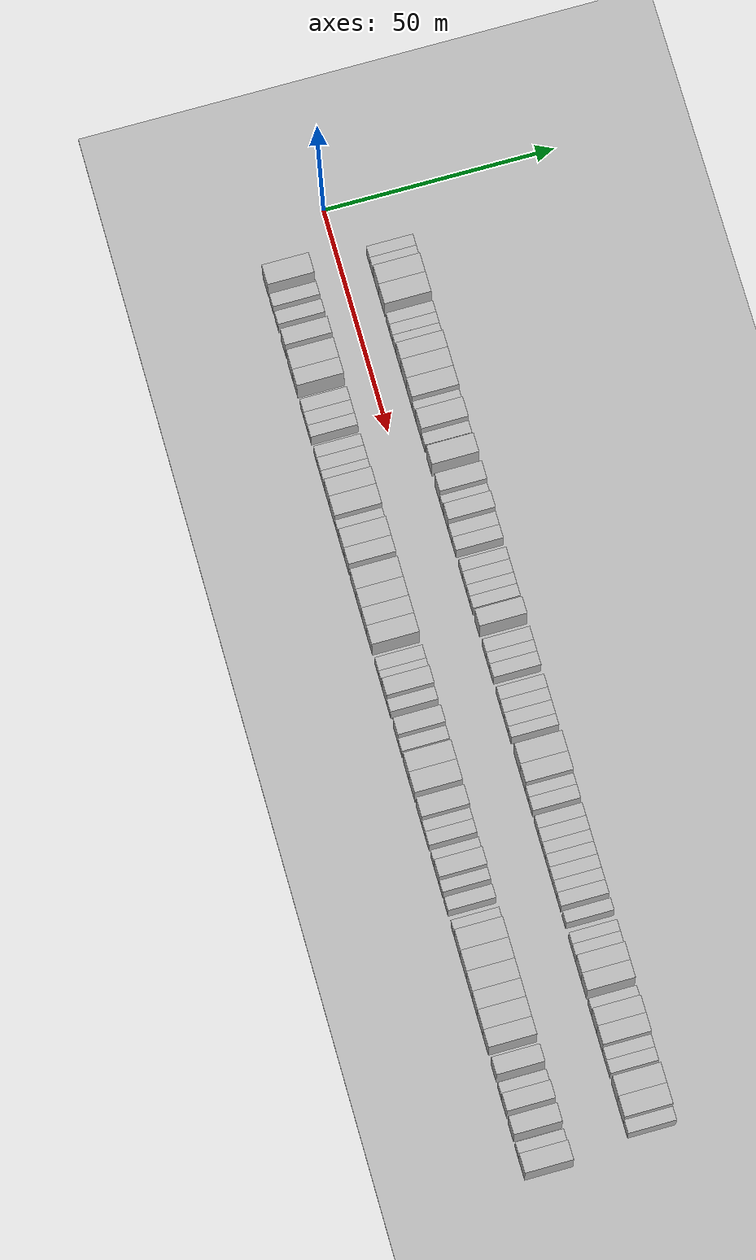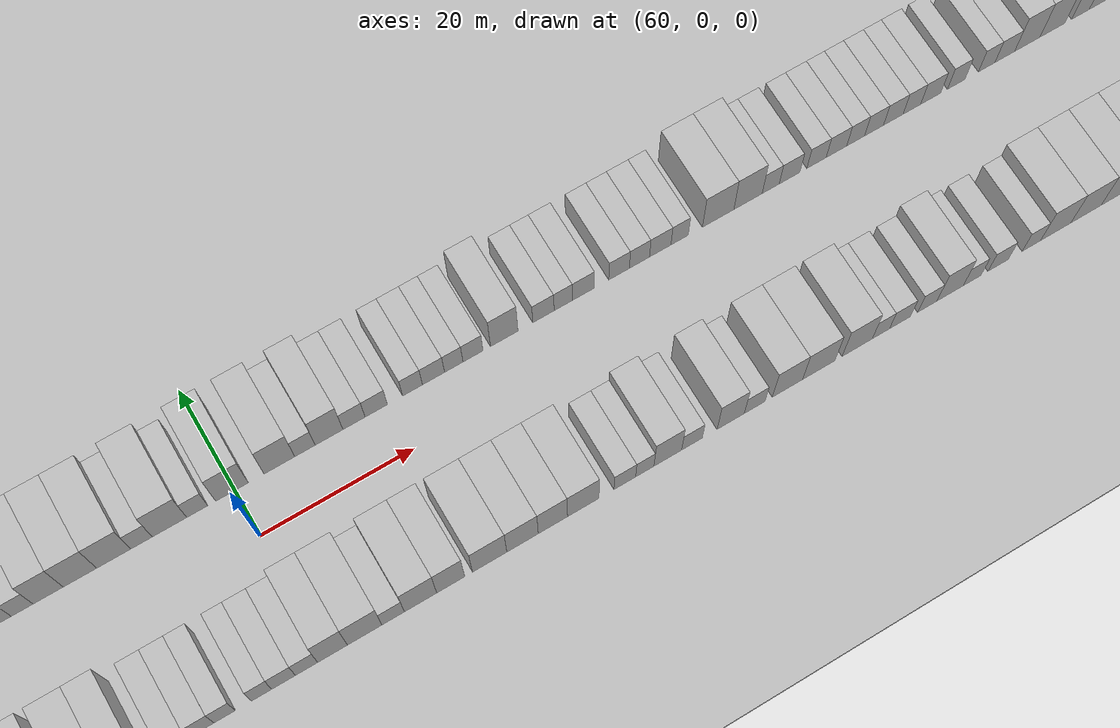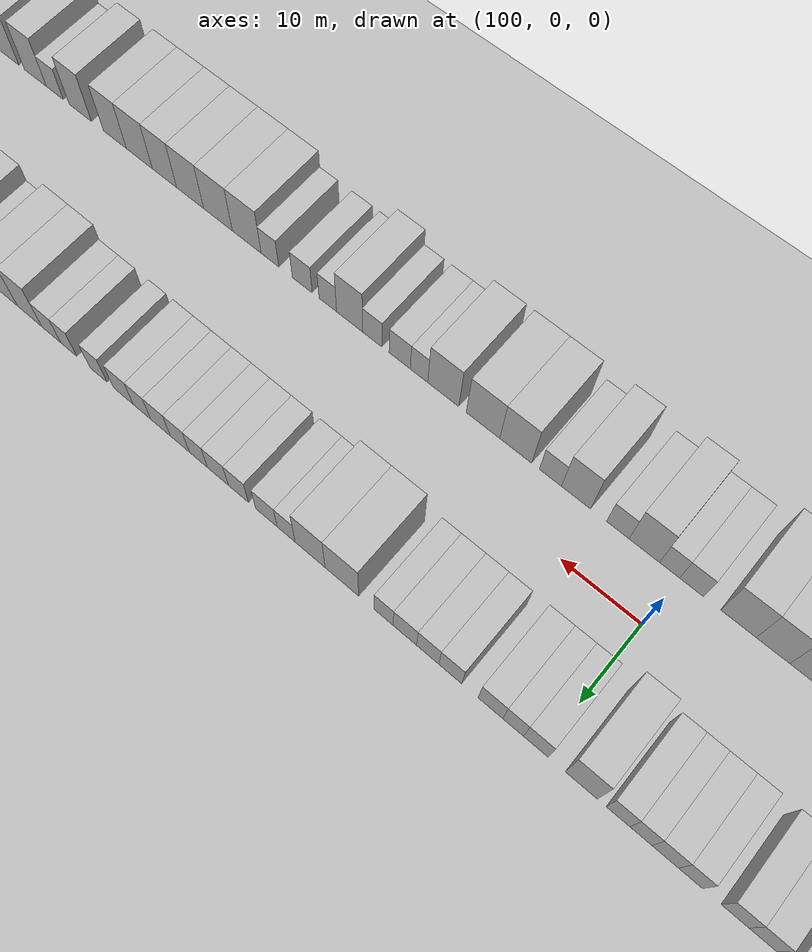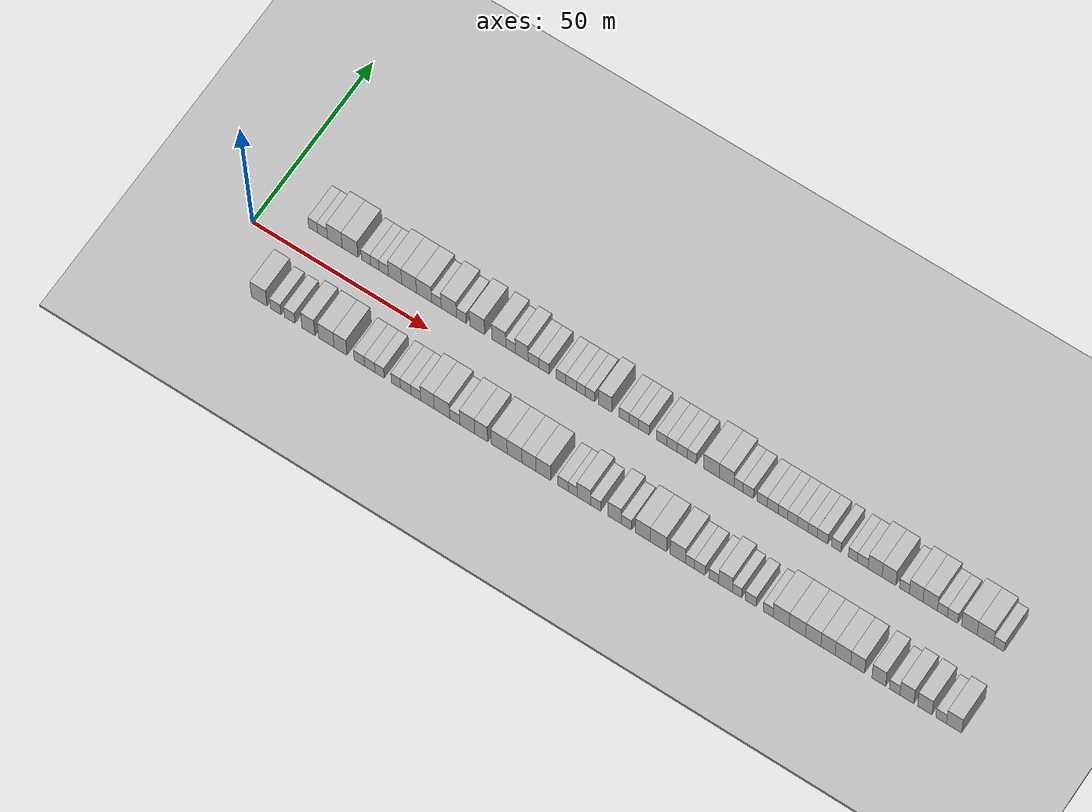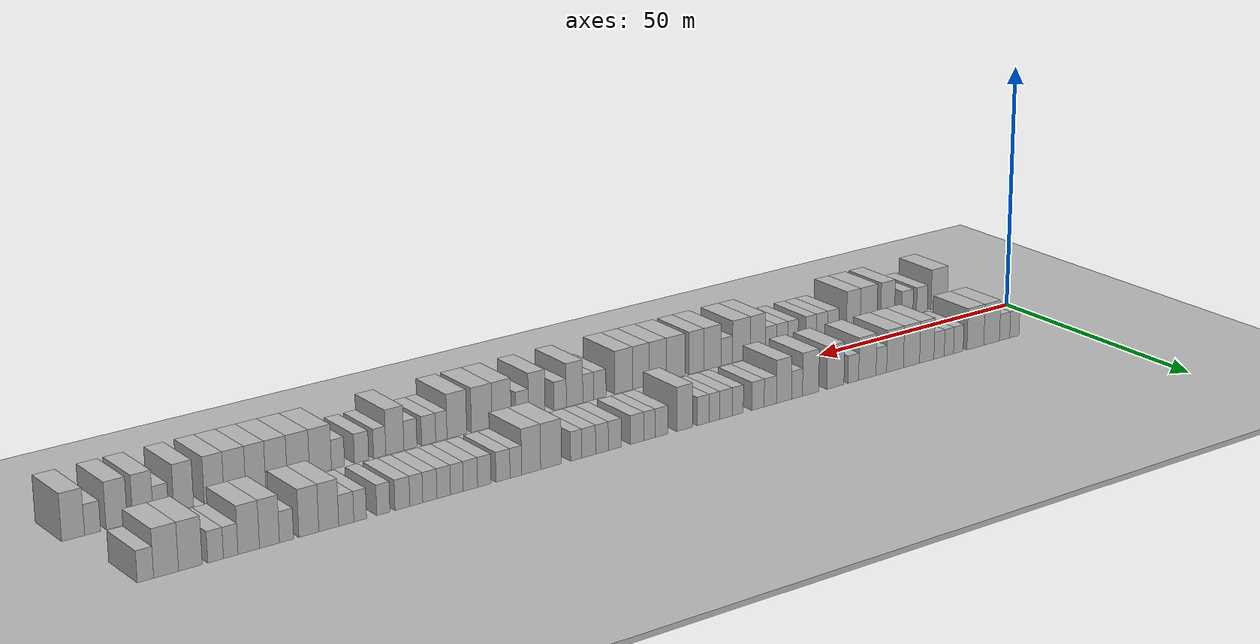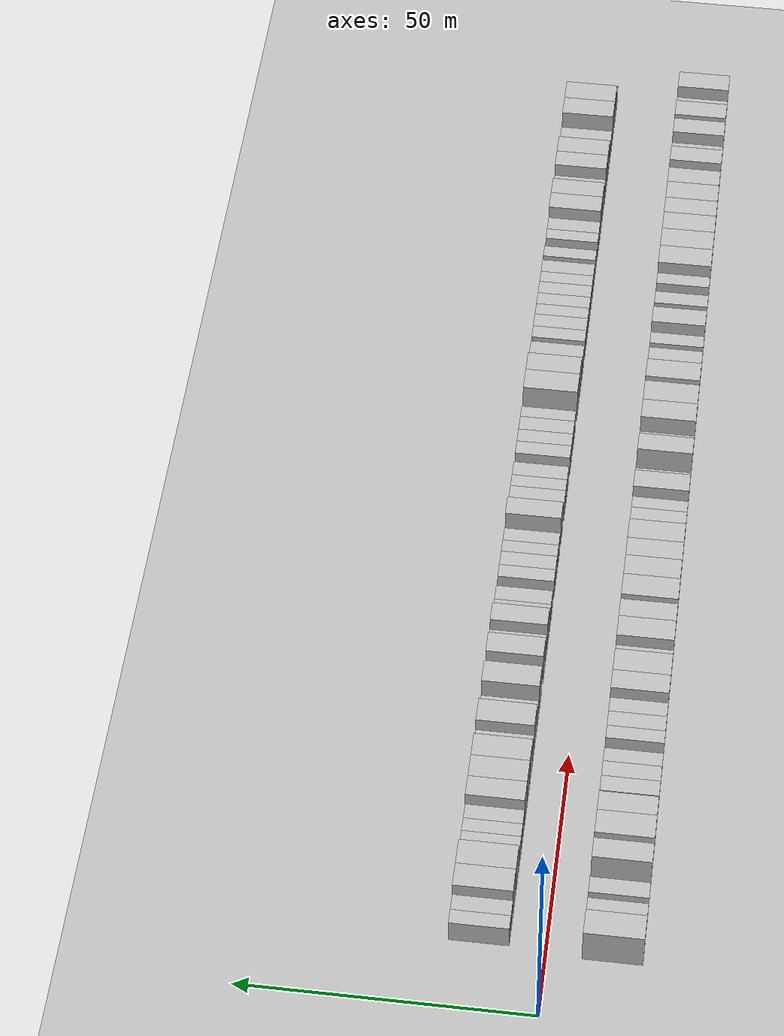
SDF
<?xml version="1.0" encoding="utf-8"?>

<sdf version="1.6">

   <world name="default">

      <gui fullscreen="0">

         <camera name="user_camera">

            <pose>-15 0 4.57585 0 0 0</pose>

            <view_controller>orbit</view_controller>

         </camera>

      </gui>

      <scene>

         <sky>

           <clouds>

             <speed>12</speed>

           </clouds>

         </sky>

         <ambient>0.4 0.4 0.4 1</ambient>

         <background>0.7 0.7 0.7 1</background>

         <shadows>1</shadows>

      </scene>

      <gravity>0 0 -9.8066</gravity>

      <magnetic_field>6e-06 2.3e-05 -4.2e-05</magnetic_field>

      <physics default="0" name="default_physics" type="ode">

         <ode>

            <solver>

               <type>quick</type>

               <iters>10</iters>

               <sor>1.0</sor>

               <use_dynamic_moi_rescaling>0</use_dynamic_moi_rescaling>

            </solver>

            <constraints>

               <cfm>0</cfm>

               <erp>0.2</erp>

               <contact_max_correcting_vel>100</contact_max_correcting_vel>

               <contact_surface_layer>0.001</contact_surface_layer>

            </constraints>

         </ode>

         <max_step_size>0.004</max_step_size>

         <real_time_factor>1</real_time_factor>

         <real_time_update_rate>250</real_time_update_rate>

      </physics>

      <light name="sun" type="directional">

         <cast_shadows>1</cast_shadows>

         <pose>0 0 10 0 0 0</pose>

         <diffuse>0.8 0.8 0.8 1</diffuse>

         <specular>0.2 0.2 0.2 1</specular>

         <attenuation>

            <range>1000</range>

            <constant>0.9</constant>

            <linear>0.01</linear>

            <quadratic>0.001</quadratic>

         </attenuation>

         <direction>-0.5 0.1 -0.9</direction>

      </light>

      <include>

         <name>ground_plane_1</name>

         <uri>model://HANNAS_ground_plane</uri>

         <pose>0 0 0  0 0 0</pose>

      </include>

      <include>

         <name>ground_plane_2</name>

         <uri>model://HANNAS_ground_plane</uri>

         <pose>100 0 0  0 0 0</pose>

      </include>

      <model name="building_1">

         <static>1</static>

         <pose frame="">13.2620 11.0000 0 0.000000 0.000000 1.570796</pose>

         <link name="link">

            <pose frame="">0 0 3.00 0 0 0</pose>

            <collision name="collision">

               <geometry>

                  <box>

                     <size>10.0000 2.5239 6.0000</size>

                  </box>

               </geometry>

               <max_contacts>10</max_contacts>

               <surface>

                  <contact>

                     <ode/>

                  </contact>

                  <bounce/>

                  <friction>

                     <torsional>

                        <ode/>

                     </torsional>

                     <ode/>

                  </friction>

               </surface>

            </collision>

            <visual name="visual">

               <cast_shadows>0</cast_shadows>

               <geometry>

                  <box>

                     <size>10.0000 2.5239 6.0000</size>

                  </box>

               </geometry>

               <material>

                  <script>

                     <uri>model://HANNAS_wall/materials/scripts</uri>

                     <uri>model://HANNAS_wall/materials/textures</uri>

                     <name>vrc/HANNAS_wall</name>

                  </script>

               </material>

            </visual>

            <self_collide>0</self_collide>

            <enable_wind>0</enable_wind>

            <kinematic>0</kinematic>

         </link>

      </model>

      <model name="building_2">

         <static>1</static>

         <pose frame="">15.9279 11.0000 0 0.000000 0.000000 1.570796</pose>

         <link name="link">

            <pose frame="">0 0 3.00 0 0 0</pose>

            <collision name="collision">

               <geometry>

                  <box>

                     <size>10.0000 2.8079 6.0000</size>

                  </box>

               </geometry>

               <max_contacts>10</max_contacts>

               <surface>

                  <contact>

                     <ode/>

                  </contact>

                  <bounce/>

                  <friction>

                     <torsional>

                        <ode/>

                     </torsional>

                     <ode/>

                  </friction>

               </surface>

            </collision>

            <visual name="visual">

               <cast_shadows>0</cast_shadows>

               <geometry>

                  <box>

                     <size>10.0000 2.8079 6.0000</size>

                  </box>

               </geometry>

               <material>

                  <script>

                     <uri>model://HANNAS_wall/materials/scripts</uri>

                     <uri>model://HANNAS_wall/materials/textures</uri>

                     <name>vrc/HANNAS_wall</name>

                  </script>

               </material>

            </visual>

            <self_collide>0</self_collide>

            <enable_wind>0</enable_wind>

            <kinematic>0</kinematic>

         </link>

      </model>

      <model name="building_3">

         <static>1</static>

         <pose frame="">19.4337 11.0000 0 0.000000 0.000000 1.570796</pose>

         <link name="link">

            <pose frame="">0 0 4.50 0 0 0</pose>

            <collision name="collision">

               <geometry>

                  <box>

                     <size>10.0000 4.2038 9.0000</size>

                  </box>

               </geometry>

               <max_contacts>10</max_contacts>

               <surface>

                  <contact>

                     <ode/>

                  </contact>

                  <bounce/>

                  <friction>

                     <torsional>

                        <ode/>

                     </torsional>

                     <ode/>

                  </friction>

               </surface>

            </collision>

            <visual name="visual">

               <cast_shadows>0</cast_shadows>

               <geometry>

                  <box>

                     <size>10.0000 4.2038 9.0000</size>

                  </box>

               </geometry>

               <material>

                  <script>

                     <uri>model://HANNAS_wall/materials/scripts</uri>

                     <uri>model://HANNAS_wall/materials/textures</uri>

                     <name>vrc/HANNAS_wall</name>

                  </script>

               </material>

            </visual>

            <self_collide>0</self_collide>

            <enable_wind>0</enable_wind>

            <kinematic>0</kinematic>

         </link>

      </model>

      <model name="building_4">

         <static>1</static>

         <pose frame="">23.7834 11.0000 0 0.000000 0.000000 1.570796</pose>

         <link name="link">

            <pose frame="">0 0 4.50 0 0 0</pose>

            <collision name="collision">

               <geometry>

                  <box>

                     <size>10.0000 4.4956 9.0000</size>

                  </box>

               </geometry>

               <max_contacts>10</max_contacts>

               <surface>

                  <contact>

                     <ode/>

                  </contact>

                  <bounce/>

                  <friction>

                     <torsional>

                        <ode/>

                     </torsional>

                     <ode/>

                  </friction>

               </surface>

            </collision>

            <visual name="visual">

               <cast_shadows>0</cast_shadows>

               <geometry>

                  <box>

                     <size>10.0000 4.4956 9.0000</size>

                  </box>

               </geometry>

               <material>

                  <script>

                     <uri>model://HANNAS_wall/materials/scripts</uri>

                     <uri>model://HANNAS_wall/materials/textures</uri>

                     <name>vrc/HANNAS_wall</name>

                  </script>

               </material>

            </visual>

            <self_collide>0</self_collide>

            <enable_wind>0</enable_wind>

            <kinematic>0</kinematic>

         </link>

      </model>

      <model name="building_5">

         <static>1</static>

         <pose frame="">28.2973 11.0000 0 0.000000 0.000000 1.570796</pose>

         <link name="link">

            <pose frame="">0 0 3.00 0 0 0</pose>

            <collision name="collision">

               <geometry>

                  <box>

                     <size>10.0000 2.5322 6.0000</size>

                  </box>

               </geometry>

               <max_contacts>10</max_contacts>

               <surface>

                  <contact>

                     <ode/>

                  </contact>

                  <bounce/>

                  <friction>

                     <torsional>

                        <ode/>

                     </torsional>

                     <ode/>

                  </friction>

               </surface>

            </collision>

            <visual name="visual">

               <cast_shadows>0</cast_shadows>

               <geometry>

                  <box>

                     <size>10.0000 2.5322 6.0000</size>

                  </box>

               </geometry>

               <material>

                  <script>

                     <uri>model://HANNAS_wall/materials/scripts</uri>

                     <uri>model://HANNAS_wall/materials/textures</uri>

                     <name>vrc/HANNAS_wall</name>

                  </script>

               </material>

            </visual>

            <self_collide>0</self_collide>

            <enable_wind>0</enable_wind>

            <kinematic>0</kinematic>

         </link>

      </model>

      <model name="building_6">

         <static>1</static>

         <pose frame="">30.7868 11.0000 0 0.000000 0.000000 1.570796</pose>

         <link name="link">

            <pose frame="">0 0 3.00 0 0 0</pose>

            <collision name="collision">

               <geometry>

                  <box>

                     <size>10.0000 2.4468 6.0000</size>

                  </box>

               </geometry>

               <max_contacts>10</max_contacts>

               <surface>

                  <contact>

                     <ode/>

                  </contact>

                  <bounce/>

                  <friction>

                     <torsional>

                        <ode/>

                     </torsional>

                     <ode/>

                  </friction>

               </surface>

            </collision>

            <visual name="visual">

               <cast_shadows>0</cast_shadows>

               <geometry>

                  <box>

                     <size>10.0000 2.4468 6.0000</size>

                  </box>

               </geometry>

               <material>

                  <script>

                     <uri>model://HANNAS_wall/materials/scripts</uri>

                     <uri>model://HANNAS_wall/materials/textures</uri>

                     <name>vrc/HANNAS_wall</name>

                  </script>

               </material>

            </visual>

            <self_collide>0</self_collide>

            <enable_wind>0</enable_wind>

            <kinematic>0</kinematic>

         </link>

      </model>

      <model name="building_7">

         <static>1</static>

         <pose frame="">33.3563 11.0000 0 0.000000 0.000000 1.570796</pose>

         <link name="link">

            <pose frame="">0 0 3.00 0 0 0</pose>

            <collision name="collision">

               <geometry>

                  <box>

                     <size>10.0000 2.6920 6.0000</size>

                  </box>

               </geometry>

               <max_contacts>10</max_contacts>

               <surface>

                  <contact>

                     <ode/>

                  </contact>

                  <bounce/>

                  <friction>

                     <torsional>

                        <ode/>

                     </torsional>

                     <ode/>

                  </friction>

               </surface>

            </collision>

            <visual name="visual">

               <cast_shadows>0</cast_shadows>

               <geometry>

                  <box>

                     <size>10.0000 2.6920 6.0000</size>

                  </box>

               </geometry>

               <material>

                  <script>

                     <uri>model://HANNAS_wall/materials/scripts</uri>

                     <uri>model://HANNAS_wall/materials/textures</uri>

                     <name>vrc/HANNAS_wall</name>

                  </script>

               </material>

            </visual>

            <self_collide>0</self_collide>

            <enable_wind>0</enable_wind>

            <kinematic>0</kinematic>

         </link>

      </model>

      <model name="building_8">

         <static>1</static>

         <pose frame="">36.5656 11.0000 0 0.000000 0.000000 1.570796</pose>

         <link name="link">

            <pose frame="">0 0 4.50 0 0 0</pose>

            <collision name="collision">

               <geometry>

                  <box>

                     <size>10.0000 3.7267 9.0000</size>

                  </box>

               </geometry>

               <max_contacts>10</max_contacts>

               <surface>

                  <contact>

                     <ode/>

                  </contact>

                  <bounce/>

                  <friction>

                     <torsional>

                        <ode/>

                     </torsional>

                     <ode/>

                  </friction>

               </surface>

            </collision>

            <visual name="visual">

               <cast_shadows>0</cast_shadows>

               <geometry>

                  <box>

                     <size>10.0000 3.7267 9.0000</size>

                  </box>

               </geometry>

               <material>

                  <script>

                     <uri>model://HANNAS_wall/materials/scripts</uri>

                     <uri>model://HANNAS_wall/materials/textures</uri>

                     <name>vrc/HANNAS_wall</name>

                  </script>

               </material>

            </visual>

            <self_collide>0</self_collide>

            <enable_wind>0</enable_wind>

            <kinematic>0</kinematic>

         </link>

      </model>

      <model name="building_9">

         <static>1</static>

         <pose frame="">40.5129 11.0000 0 0.000000 0.000000 1.570796</pose>

         <link name="link">

            <pose frame="">0 0 4.50 0 0 0</pose>

            <collision name="collision">

               <geometry>

                  <box>

                     <size>10.0000 4.1679 9.0000</size>

                  </box>

               </geometry>

               <max_contacts>10</max_contacts>

               <surface>

                  <contact>

                     <ode/>

                  </contact>

                  <bounce/>

                  <friction>

                     <torsional>

                        <ode/>

                     </torsional>

                     <ode/>

                  </friction>

               </surface>

            </collision>

            <visual name="visual">

               <cast_shadows>0</cast_shadows>

               <geometry>

                  <box>

                     <size>10.0000 4.1679 9.0000</size>

                  </box>

               </geometry>

               <material>

                  <script>

                     <uri>model://HANNAS_wall/materials/scripts</uri>

                     <uri>model://HANNAS_wall/materials/textures</uri>

                     <name>vrc/HANNAS_wall</name>

                  </script>

               </material>

            </visual>

            <self_collide>0</self_collide>

            <enable_wind>0</enable_wind>

            <kinematic>0</kinematic>

         </link>

      </model>

      <model name="building_10">

         <static>1</static>

         <pose frame="">44.7344 11.0000 0 0.000000 0.000000 1.570796</pose>

         <link name="link">

            <pose frame="">0 0 4.50 0 0 0</pose>

            <collision name="collision">

               <geometry>

                  <box>

                     <size>10.0000 4.2751 9.0000</size>

                  </box>

               </geometry>

               <max_contacts>10</max_contacts>

               <surface>

                  <contact>

                     <ode/>

                  </contact>

                  <bounce/>

                  <friction>

                     <torsional>

                        <ode/>

                     </torsional>

                     <ode/>

                  </friction>

               </surface>

            </collision>

            <visual name="visual">

               <cast_shadows>0</cast_shadows>

               <geometry>

                  <box>

                     <size>10.0000 4.2751 9.0000</size>

                  </box>

               </geometry>

               <material>

                  <script>

                     <uri>model://HANNAS_wall/materials/scripts</uri>

                     <uri>model://HANNAS_wall/materials/textures</uri>

                     <name>vrc/HANNAS_wall</name>

                  </script>

               </material>

            </visual>

            <self_collide>0</self_collide>

            <enable_wind>0</enable_wind>

            <kinematic>0</kinematic>

         </link>

      </model>

      <model name="building_11">

         <static>1</static>

         <pose frame="">48.2153 11.0000 0 0.000000 0.000000 1.570796</pose>

         <link name="link">

            <pose frame="">0 0 3.00 0 0 0</pose>

            <collision name="collision">

               <geometry>

                  <box>

                     <size>10.0000 2.6868 6.0000</size>

                  </box>

               </geometry>

               <max_contacts>10</max_contacts>

               <surface>

                  <contact>

                     <ode/>

                  </contact>

                  <bounce/>

                  <friction>

                     <torsional>

                        <ode/>

                     </torsional>

                     <ode/>

                  </friction>

               </surface>

            </collision>

            <visual name="visual">

               <cast_shadows>0</cast_shadows>

               <geometry>

                  <box>

                     <size>10.0000 2.6868 6.0000</size>

                  </box>

               </geometry>

               <material>

                  <script>

                     <uri>model://HANNAS_wall/materials/scripts</uri>

                     <uri>model://HANNAS_wall/materials/textures</uri>

                     <name>vrc/HANNAS_wall</name>

                  </script>

               </material>

            </visual>

            <self_collide>0</self_collide>

            <enable_wind>0</enable_wind>

            <kinematic>0</kinematic>

         </link>

      </model>

      <model name="building_12">

         <static>1</static>

         <pose frame="">51.7412 11.0000 0 0.000000 0.000000 1.570796</pose>

         <link name="link">

            <pose frame="">0 0 4.50 0 0 0</pose>

            <collision name="collision">

               <geometry>

                  <box>

                     <size>10.0000 4.3649 9.0000</size>

                  </box>

               </geometry>

               <max_contacts>10</max_contacts>

               <surface>

                  <contact>

                     <ode/>

                  </contact>

                  <bounce/>

                  <friction>

                     <torsional>

                        <ode/>

                     </torsional>

                     <ode/>

                  </friction>

               </surface>

            </collision>

            <visual name="visual">

               <cast_shadows>0</cast_shadows>

               <geometry>

                  <box>

                     <size>10.0000 4.3649 9.0000</size>

                  </box>

               </geometry>

               <material>

                  <script>

                     <uri>model://HANNAS_wall/materials/scripts</uri>

                     <uri>model://HANNAS_wall/materials/textures</uri>

                     <name>vrc/HANNAS_wall</name>

                  </script>

               </material>

            </visual>

            <self_collide>0</self_collide>

            <enable_wind>0</enable_wind>

            <kinematic>0</kinematic>

         </link>

      </model>

      <model name="building_13">

         <static>1</static>

         <pose frame="">55.2586 11.0000 0 0.000000 0.000000 1.570796</pose>

         <link name="link">

            <pose frame="">0 0 3.00 0 0 0</pose>

            <collision name="collision">

               <geometry>

                  <box>

                     <size>10.0000 2.6699 6.0000</size>

                  </box>

               </geometry>

               <max_contacts>10</max_contacts>

               <surface>

                  <contact>

                     <ode/>

                  </contact>

                  <bounce/>

                  <friction>

                     <torsional>

                        <ode/>

                     </torsional>

                     <ode/>

                  </friction>

               </surface>

            </collision>

            <visual name="visual">

               <cast_shadows>0</cast_shadows>

               <geometry>

                  <box>

                     <size>10.0000 2.6699 6.0000</size>

                  </box>

               </geometry>

               <material>

                  <script>

                     <uri>model://HANNAS_wall/materials/scripts</uri>

                     <uri>model://HANNAS_wall/materials/textures</uri>

                     <name>vrc/HANNAS_wall</name>

                  </script>

               </material>

            </visual>

            <self_collide>0</self_collide>

            <enable_wind>0</enable_wind>

            <kinematic>0</kinematic>

         </link>

      </model>

      <model name="building_14">

         <static>1</static>

         <pose frame="">59.6902 11.0000 0 0.000000 0.000000 1.570796</pose>

         <link name="link">

            <pose frame="">0 0 4.50 0 0 0</pose>

            <collision name="collision">

               <geometry>

                  <box>

                     <size>10.0000 4.1933 9.0000</size>

                  </box>

               </geometry>

               <max_contacts>10</max_contacts>

               <surface>

                  <contact>

                     <ode/>

                  </contact>

                  <bounce/>

                  <friction>

                     <torsional>

                        <ode/>

                     </torsional>

                     <ode/>

                  </friction>

               </surface>

            </collision>

            <visual name="visual">

               <cast_shadows>0</cast_shadows>

               <geometry>

                  <box>

                     <size>10.0000 4.1933 9.0000</size>

                  </box>

               </geometry>

               <material>

                  <script>

                     <uri>model://HANNAS_wall/materials/scripts</uri>

                     <uri>model://HANNAS_wall/materials/textures</uri>

                     <name>vrc/HANNAS_wall</name>

                  </script>

               </material>

            </visual>

            <self_collide>0</self_collide>

            <enable_wind>0</enable_wind>

            <kinematic>0</kinematic>

         </link>

      </model>

      <model name="building_15">

         <static>1</static>

         <pose frame="">65.7693 11.0000 0 0.000000 0.000000 1.570796</pose>

         <link name="link">

            <pose frame="">0 0 4.50 0 0 0</pose>

            <collision name="collision">

               <geometry>

                  <box>

                     <size>10.0000 3.9649 9.0000</size>

                  </box>

               </geometry>

               <max_contacts>10</max_contacts>

               <surface>

                  <contact>

                     <ode/>

                  </contact>

                  <bounce/>

                  <friction>

                     <torsional>

                        <ode/>

                     </torsional>

                     <ode/>

                  </friction>

               </surface>

            </collision>

            <visual name="visual">

               <cast_shadows>0</cast_shadows>

               <geometry>

                  <box>

                     <size>10.0000 3.9649 9.0000</size>

                  </box>

               </geometry>

               <material>

                  <script>

                     <uri>model://HANNAS_wall/materials/scripts</uri>

                     <uri>model://HANNAS_wall/materials/textures</uri>

                     <name>vrc/HANNAS_wall</name>

                  </script>

               </material>

            </visual>

            <self_collide>0</self_collide>

            <enable_wind>0</enable_wind>

            <kinematic>0</kinematic>

         </link>

      </model>

      <model name="building_16">

         <static>1</static>

         <pose frame="">69.0763 11.0000 0 0.000000 0.000000 1.570796</pose>

         <link name="link">

            <pose frame="">0 0 3.00 0 0 0</pose>

            <collision name="collision">

               <geometry>

                  <box>

                     <size>10.0000 2.6493 6.0000</size>

                  </box>

               </geometry>

               <max_contacts>10</max_contacts>

               <surface>

                  <contact>

                     <ode/>

                  </contact>

                  <bounce/>

                  <friction>

                     <torsional>

                        <ode/>

                     </torsional>

                     <ode/>

                  </friction>

               </surface>

            </collision>

            <visual name="visual">

               <cast_shadows>0</cast_shadows>

               <geometry>

                  <box>

                     <size>10.0000 2.6493 6.0000</size>

                  </box>

               </geometry>

               <material>

                  <script>

                     <uri>model://HANNAS_wall/materials/scripts</uri>

                     <uri>model://HANNAS_wall/materials/textures</uri>

                     <name>vrc/HANNAS_wall</name>

                  </script>

               </material>

            </visual>

            <self_collide>0</self_collide>

            <enable_wind>0</enable_wind>

            <kinematic>0</kinematic>

         </link>

      </model>

      <model name="building_17">

         <static>1</static>

         <pose frame="">72.2110 11.0000 0 0.000000 0.000000 1.570796</pose>

         <link name="link">

            <pose frame="">0 0 4.50 0 0 0</pose>

            <collision name="collision">

               <geometry>

                  <box>

                     <size>10.0000 3.6201 9.0000</size>

                  </box>

               </geometry>

               <max_contacts>10</max_contacts>

               <surface>

                  <contact>

                     <ode/>

                  </contact>

                  <bounce/>

                  <friction>

                     <torsional>

                        <ode/>

                     </torsional>

                     <ode/>

                  </friction>

               </surface>

            </collision>

            <visual name="visual">

               <cast_shadows>0</cast_shadows>

               <geometry>

                  <box>

                     <size>10.0000 3.6201 9.0000</size>

                  </box>

               </geometry>

               <material>

                  <script>

                     <uri>model://HANNAS_wall/materials/scripts</uri>

                     <uri>model://HANNAS_wall/materials/textures</uri>

                     <name>vrc/HANNAS_wall</name>

                  </script>

               </material>

            </visual>

            <self_collide>0</self_collide>

            <enable_wind>0</enable_wind>

            <kinematic>0</kinematic>

         </link>

      </model>

      <model name="building_18">

         <static>1</static>

         <pose frame="">75.4774 11.0000 0 0.000000 0.000000 1.570796</pose>

         <link name="link">

            <pose frame="">0 0 3.00 0 0 0</pose>

            <collision name="collision">

               <geometry>

                  <box>

                     <size>10.0000 2.9127 6.0000</size>

                  </box>

               </geometry>

               <max_contacts>10</max_contacts>

               <surface>

                  <contact>

                     <ode/>

                  </contact>

                  <bounce/>

                  <friction>

                     <torsional>

                        <ode/>

                     </torsional>

                     <ode/>

                  </friction>

               </surface>

            </collision>

            <visual name="visual">

               <cast_shadows>0</cast_shadows>

               <geometry>

                  <box>

                     <size>10.0000 2.9127 6.0000</size>

                  </box>

               </geometry>

               <material>

                  <script>

                     <uri>model://HANNAS_wall/materials/scripts</uri>

                     <uri>model://HANNAS_wall/materials/textures</uri>

                     <name>vrc/HANNAS_wall</name>

                  </script>

               </material>

            </visual>

            <self_collide>0</self_collide>

            <enable_wind>0</enable_wind>

            <kinematic>0</kinematic>

         </link>

      </model>

      <model name="building_19">

         <static>1</static>

         <pose frame="">78.4027 11.0000 0 0.000000 0.000000 1.570796</pose>

         <link name="link">

            <pose frame="">0 0 3.00 0 0 0</pose>

            <collision name="collision">

               <geometry>

                  <box>

                     <size>10.0000 2.9378 6.0000</size>

                  </box>

               </geometry>

               <max_contacts>10</max_contacts>

               <surface>

                  <contact>

                     <ode/>

                  </contact>

                  <bounce/>

                  <friction>

                     <torsional>

                        <ode/>

                     </torsional>

                     <ode/>

                  </friction>

               </surface>

            </collision>

            <visual name="visual">

               <cast_shadows>0</cast_shadows>

               <geometry>

                  <box>

                     <size>10.0000 2.9378 6.0000</size>

                  </box>

               </geometry>

               <material>

                  <script>

                     <uri>model://HANNAS_wall/materials/scripts</uri>

                     <uri>model://HANNAS_wall/materials/textures</uri>

                     <name>vrc/HANNAS_wall</name>

                  </script>

               </material>

            </visual>

            <self_collide>0</self_collide>

            <enable_wind>0</enable_wind>

            <kinematic>0</kinematic>

         </link>

      </model>

      <model name="building_20">

         <static>1</static>

         <pose frame="">83.1809 11.0000 0 0.000000 0.000000 1.570796</pose>

         <link name="link">

            <pose frame="">0 0 3.00 0 0 0</pose>

            <collision name="collision">

               <geometry>

                  <box>

                     <size>10.0000 2.6186 6.0000</size>

                  </box>

               </geometry>

               <max_contacts>10</max_contacts>

               <surface>

                  <contact>

                     <ode/>

                  </contact>

                  <bounce/>

                  <friction>

                     <torsional>

                        <ode/>

                     </torsional>

                     <ode/>

                  </friction>

               </surface>

            </collision>

            <visual name="visual">

               <cast_shadows>0</cast_shadows>

               <geometry>

                  <box>

                     <size>10.0000 2.6186 6.0000</size>

                  </box>

               </geometry>

               <material>

                  <script>

                     <uri>model://HANNAS_wall/materials/scripts</uri>

                     <uri>model://HANNAS_wall/materials/textures</uri>

                     <name>vrc/HANNAS_wall</name>

                  </script>

               </material>

            </visual>

            <self_collide>0</self_collide>

            <enable_wind>0</enable_wind>

            <kinematic>0</kinematic>

         </link>

      </model>

      <model name="building_21">

         <static>1</static>

         <pose frame="">85.9597 11.0000 0 0.000000 0.000000 1.570796</pose>

         <link name="link">

            <pose frame="">0 0 3.00 0 0 0</pose>

            <collision name="collision">

               <geometry>

                  <box>

                     <size>10.0000 2.9390 6.0000</size>

                  </box>

               </geometry>

               <max_contacts>10</max_contacts>

               <surface>

                  <contact>

                     <ode/>

                  </contact>

                  <bounce/>

                  <friction>

                     <torsional>

                        <ode/>

                     </torsional>

                     <ode/>

                  </friction>

               </surface>

            </collision>

            <visual name="visual">

               <cast_shadows>0</cast_shadows>

               <geometry>

                  <box>

                     <size>10.0000 2.9390 6.0000</size>

                  </box>

               </geometry>

               <material>

                  <script>

                     <uri>model://HANNAS_wall/materials/scripts</uri>

                     <uri>model://HANNAS_wall/materials/textures</uri>

                     <name>vrc/HANNAS_wall</name>

                  </script>

               </material>

            </visual>

            <self_collide>0</self_collide>

            <enable_wind>0</enable_wind>

            <kinematic>0</kinematic>

         </link>

      </model>

      <model name="building_22">

         <static>1</static>

         <pose frame="">88.6593 11.0000 0 0.000000 0.000000 1.570796</pose>

         <link name="link">

            <pose frame="">0 0 3.00 0 0 0</pose>

            <collision name="collision">

               <geometry>

                  <box>

                     <size>10.0000 2.4602 6.0000</size>

                  </box>

               </geometry>

               <max_contacts>10</max_contacts>

               <surface>

                  <contact>

                     <ode/>

                  </contact>

                  <bounce/>

                  <friction>

                     <torsional>

                        <ode/>

                     </torsional>

                     <ode/>

                  </friction>

               </surface>

            </collision>

            <visual name="visual">

               <cast_shadows>0</cast_shadows>

               <geometry>

                  <box>

                     <size>10.0000 2.4602 6.0000</size>

                  </box>

               </geometry>

               <material>

                  <script>

                     <uri>model://HANNAS_wall/materials/scripts</uri>

                     <uri>model://HANNAS_wall/materials/textures</uri>

                     <name>vrc/HANNAS_wall</name>

                  </script>

               </material>

            </visual>

            <self_collide>0</self_collide>

            <enable_wind>0</enable_wind>

            <kinematic>0</kinematic>

         </link>

      </model>

      <model name="building_23">

         <static>1</static>

         <pose frame="">91.2273 11.0000 0 0.000000 0.000000 1.570796</pose>

         <link name="link">

            <pose frame="">0 0 3.00 0 0 0</pose>

            <collision name="collision">

               <geometry>

                  <box>

                     <size>10.0000 2.6759 6.0000</size>

                  </box>

               </geometry>

               <max_contacts>10</max_contacts>

               <surface>

                  <contact>

                     <ode/>

                  </contact>

                  <bounce/>

                  <friction>

                     <torsional>

                        <ode/>

                     </torsional>

                     <ode/>

                  </friction>

               </surface>

            </collision>

            <visual name="visual">

               <cast_shadows>0</cast_shadows>

               <geometry>

                  <box>

                     <size>10.0000 2.6759 6.0000</size>

                  </box>

               </geometry>

               <material>

                  <script>

                     <uri>model://HANNAS_wall/materials/scripts</uri>

                     <uri>model://HANNAS_wall/materials/textures</uri>

                     <name>vrc/HANNAS_wall</name>

                  </script>

               </material>

            </visual>

            <self_collide>0</self_collide>

            <enable_wind>0</enable_wind>

            <kinematic>0</kinematic>

         </link>

      </model>

      <model name="building_24">

         <static>1</static>

         <pose frame="">95.4174 11.0000 0 0.000000 0.000000 1.570796</pose>

         <link name="link">

            <pose frame="">0 0 4.50 0 0 0</pose>

            <collision name="collision">

               <geometry>

                  <box>

                     <size>10.0000 3.7043 9.0000</size>

                  </box>

               </geometry>

               <max_contacts>10</max_contacts>

               <surface>

                  <contact>

                     <ode/>

                  </contact>

                  <bounce/>

                  <friction>

                     <torsional>

                        <ode/>

                     </torsional>

                     <ode/>

                  </friction>

               </surface>

            </collision>

            <visual name="visual">

               <cast_shadows>0</cast_shadows>

               <geometry>

                  <box>

                     <size>10.0000 3.7043 9.0000</size>

                  </box>

               </geometry>

               <material>

                  <script>

                     <uri>model://HANNAS_wall/materials/scripts</uri>

                     <uri>model://HANNAS_wall/materials/textures</uri>

                     <name>vrc/HANNAS_wall</name>

                  </script>

               </material>

            </visual>

            <self_collide>0</self_collide>

            <enable_wind>0</enable_wind>

            <kinematic>0</kinematic>

         </link>

      </model>

      <model name="building_25">

         <static>1</static>

         <pose frame="">100.7175 11.0000 0 0.000000 0.000000 1.570796</pose>

         <link name="link">

            <pose frame="">0 0 3.00 0 0 0</pose>

            <collision name="collision">

               <geometry>

                  <box>

                     <size>10.0000 2.8959 6.0000</size>

                  </box>

               </geometry>

               <max_contacts>10</max_contacts>

               <surface>

                  <contact>

                     <ode/>

                  </contact>

                  <bounce/>

                  <friction>

                     <torsional>

                        <ode/>

                     </torsional>

                     <ode/>

                  </friction>

               </surface>

            </collision>

            <visual name="visual">

               <cast_shadows>0</cast_shadows>

               <geometry>

                  <box>

                     <size>10.0000 2.8959 6.0000</size>

                  </box>

               </geometry>

               <material>

                  <script>

                     <uri>model://HANNAS_wall/materials/scripts</uri>

                     <uri>model://HANNAS_wall/materials/textures</uri>

                     <name>vrc/HANNAS_wall</name>

                  </script>

               </material>

            </visual>

            <self_collide>0</self_collide>

            <enable_wind>0</enable_wind>

            <kinematic>0</kinematic>

         </link>

      </model>

      <model name="building_26">

         <static>1</static>

         <pose frame="">103.4098 11.0000 0 0.000000 0.000000 1.570796</pose>

         <link name="link">

            <pose frame="">0 0 3.00 0 0 0</pose>

            <collision name="collision">

               <geometry>

                  <box>

                     <size>10.0000 2.4887 6.0000</size>

                  </box>

               </geometry>

               <max_contacts>10</max_contacts>

               <surface>

                  <contact>

                     <ode/>

                  </contact>

                  <bounce/>

                  <friction>

                     <torsional>

                        <ode/>

                     </torsional>

                     <ode/>

                  </friction>

               </surface>

            </collision>

            <visual name="visual">

               <cast_shadows>0</cast_shadows>

               <geometry>

                  <box>

                     <size>10.0000 2.4887 6.0000</size>

                  </box>

               </geometry>

               <material>

                  <script>

                     <uri>model://HANNAS_wall/materials/scripts</uri>

                     <uri>model://HANNAS_wall/materials/textures</uri>

                     <name>vrc/HANNAS_wall</name>

                  </script>

               </material>

            </visual>

            <self_collide>0</self_collide>

            <enable_wind>0</enable_wind>

            <kinematic>0</kinematic>

         </link>

      </model>

      <model name="building_27">

         <static>1</static>

         <pose frame="">106.1464 11.0000 0 0.000000 0.000000 1.570796</pose>

         <link name="link">

            <pose frame="">0 0 3.00 0 0 0</pose>

            <collision name="collision">

               <geometry>

                  <box>

                     <size>10.0000 2.9846 6.0000</size>

                  </box>

               </geometry>

               <max_contacts>10</max_contacts>

               <surface>

                  <contact>

                     <ode/>

                  </contact>

                  <bounce/>

                  <friction>

                     <torsional>

                        <ode/>

                     </torsional>

                     <ode/>

                  </friction>

               </surface>

            </collision>

            <visual name="visual">

               <cast_shadows>0</cast_shadows>

               <geometry>

                  <box>

                     <size>10.0000 2.9846 6.0000</size>

                  </box>

               </geometry>

               <material>

                  <script>

                     <uri>model://HANNAS_wall/materials/scripts</uri>

                     <uri>model://HANNAS_wall/materials/textures</uri>

                     <name>vrc/HANNAS_wall</name>

                  </script>

               </material>

            </visual>

            <self_collide>0</self_collide>

            <enable_wind>0</enable_wind>

            <kinematic>0</kinematic>

         </link>

      </model>

      <model name="building_28">

         <static>1</static>

         <pose frame="">111.0552 11.0000 0 0.000000 0.000000 1.570796</pose>

         <link name="link">

            <pose frame="">0 0 3.00 0 0 0</pose>

            <collision name="collision">

               <geometry>

                  <box>

                     <size>10.0000 2.8328 6.0000</size>

                  </box>

               </geometry>

               <max_contacts>10</max_contacts>

               <surface>

                  <contact>

                     <ode/>

                  </contact>

                  <bounce/>

                  <friction>

                     <torsional>

                        <ode/>

                     </torsional>

                     <ode/>

                  </friction>

               </surface>

            </collision>

            <visual name="visual">

               <cast_shadows>0</cast_shadows>

               <geometry>

                  <box>

                     <size>10.0000 2.8328 6.0000</size>

                  </box>

               </geometry>

               <material>

                  <script>

                     <uri>model://HANNAS_wall/materials/scripts</uri>

                     <uri>model://HANNAS_wall/materials/textures</uri>

                     <name>vrc/HANNAS_wall</name>

                  </script>

               </material>

            </visual>

            <self_collide>0</self_collide>

            <enable_wind>0</enable_wind>

            <kinematic>0</kinematic>

         </link>

      </model>

      <model name="building_29">

         <static>1</static>

         <pose frame="">113.8611 11.0000 0 0.000000 0.000000 1.570796</pose>

         <link name="link">

            <pose frame="">0 0 3.00 0 0 0</pose>

            <collision name="collision">

               <geometry>

                  <box>

                     <size>10.0000 2.7790 6.0000</size>

                  </box>

               </geometry>

               <max_contacts>10</max_contacts>

               <surface>

                  <contact>

                     <ode/>

                  </contact>

                  <bounce/>

                  <friction>

                     <torsional>

                        <ode/>

                     </torsional>

                     <ode/>

                  </friction>

               </surface>

            </collision>

            <visual name="visual">

               <cast_shadows>0</cast_shadows>

               <geometry>

                  <box>

                     <size>10.0000 2.7790 6.0000</size>

                  </box>

               </geometry>

               <material>

                  <script>

                     <uri>model://HANNAS_wall/materials/scripts</uri>

                     <uri>model://HANNAS_wall/materials/textures</uri>

                     <name>vrc/HANNAS_wall</name>

                  </script>

               </material>

            </visual>

            <self_collide>0</self_collide>

            <enable_wind>0</enable_wind>

            <kinematic>0</kinematic>

         </link>

      </model>

      <model name="building_30">

         <static>1</static>

         <pose frame="">116.7405 11.0000 0 0.000000 0.000000 1.570796</pose>

         <link name="link">

            <pose frame="">0 0 3.00 0 0 0</pose>

            <collision name="collision">

               <geometry>

                  <box>

                     <size>10.0000 2.9799 6.0000</size>

                  </box>

               </geometry>

               <max_contacts>10</max_contacts>

               <surface>

                  <contact>

                     <ode/>

                  </contact>

                  <bounce/>

                  <friction>

                     <torsional>

                        <ode/>

                     </torsional>

                     <ode/>

                  </friction>

               </surface>

            </collision>

            <visual name="visual">

               <cast_shadows>0</cast_shadows>

               <geometry>

                  <box>

                     <size>10.0000 2.9799 6.0000</size>

                  </box>

               </geometry>

               <material>

                  <script>

                     <uri>model://HANNAS_wall/materials/scripts</uri>

                     <uri>model://HANNAS_wall/materials/textures</uri>

                     <name>vrc/HANNAS_wall</name>

                  </script>

               </material>

            </visual>

            <self_collide>0</self_collide>

            <enable_wind>0</enable_wind>

            <kinematic>0</kinematic>

         </link>

      </model>

      <model name="building_31">

         <static>1</static>

         <pose frame="">119.4345 11.0000 0 0.000000 0.000000 1.570796</pose>

         <link name="link">

            <pose frame="">0 0 3.00 0 0 0</pose>

            <collision name="collision">

               <geometry>

                  <box>

                     <size>10.0000 2.4082 6.0000</size>

                  </box>

               </geometry>

               <max_contacts>10</max_contacts>

               <surface>

                  <contact>

                     <ode/>

                  </contact>

                  <bounce/>

                  <friction>

                     <torsional>

                        <ode/>

                     </torsional>

                     <ode/>

                  </friction>

               </surface>

            </collision>

            <visual name="visual">

               <cast_shadows>0</cast_shadows>

               <geometry>

                  <box>

                     <size>10.0000 2.4082 6.0000</size>

                  </box>

               </geometry>

               <material>

                  <script>

                     <uri>model://HANNAS_wall/materials/scripts</uri>

                     <uri>model://HANNAS_wall/materials/textures</uri>

                     <name>vrc/HANNAS_wall</name>

                  </script>

               </material>

            </visual>

            <self_collide>0</self_collide>

            <enable_wind>0</enable_wind>

            <kinematic>0</kinematic>

         </link>

      </model>

      <model name="building_32">

         <static>1</static>

         <pose frame="">124.8365 11.0000 0 0.000000 0.000000 1.570796</pose>

         <link name="link">

            <pose frame="">0 0 4.50 0 0 0</pose>

            <collision name="collision">

               <geometry>

                  <box>

                     <size>10.0000 4.3958 9.0000</size>

                  </box>

               </geometry>

               <max_contacts>10</max_contacts>

               <surface>

                  <contact>

                     <ode/>

                  </contact>

                  <bounce/>

                  <friction>

                     <torsional>

                        <ode/>

                     </torsional>

                     <ode/>

                  </friction>

               </surface>

            </collision>

            <visual name="visual">

               <cast_shadows>0</cast_shadows>

               <geometry>

                  <box>

                     <size>10.0000 4.3958 9.0000</size>

                  </box>

               </geometry>

               <material>

                  <script>

                     <uri>model://HANNAS_wall/materials/scripts</uri>

                     <uri>model://HANNAS_wall/materials/textures</uri>

                     <name>vrc/HANNAS_wall</name>

                  </script>

               </material>

            </visual>

            <self_collide>0</self_collide>

            <enable_wind>0</enable_wind>

            <kinematic>0</kinematic>

         </link>

      </model>

      <model name="building_33">

         <static>1</static>

         <pose frame="">129.0354 11.0000 0 0.000000 0.000000 1.570796</pose>

         <link name="link">

            <pose frame="">0 0 4.50 0 0 0</pose>

            <collision name="collision">

               <geometry>

                  <box>

                     <size>10.0000 4.0018 9.0000</size>

                  </box>

               </geometry>

               <max_contacts>10</max_contacts>

               <surface>

                  <contact>

                     <ode/>

                  </contact>

                  <bounce/>

                  <friction>

                     <torsional>

                        <ode/>

                     </torsional>

                     <ode/>

                  </friction>

               </surface>

            </collision>

            <visual name="visual">

               <cast_shadows>0</cast_shadows>

               <geometry>

                  <box>

                     <size>10.0000 4.0018 9.0000</size>

                  </box>

               </geometry>

               <material>

                  <script>

                     <uri>model://HANNAS_wall/materials/scripts</uri>

                     <uri>model://HANNAS_wall/materials/textures</uri>

                     <name>vrc/HANNAS_wall</name>

                  </script>

               </material>

            </visual>

            <self_collide>0</self_collide>

            <enable_wind>0</enable_wind>

            <kinematic>0</kinematic>

         </link>

      </model>

      <model name="building_34">

         <static>1</static>

         <pose frame="">132.2460 11.0000 0 0.000000 0.000000 1.570796</pose>

         <link name="link">

            <pose frame="">0 0 3.00 0 0 0</pose>

            <collision name="collision">

               <geometry>

                  <box>

                     <size>10.0000 2.4194 6.0000</size>

                  </box>

               </geometry>

               <max_contacts>10</max_contacts>

               <surface>

                  <contact>

                     <ode/>

                  </contact>

                  <bounce/>

                  <friction>

                     <torsional>

                        <ode/>

                     </torsional>

                     <ode/>

                  </friction>

               </surface>

            </collision>

            <visual name="visual">

               <cast_shadows>0</cast_shadows>

               <geometry>

                  <box>

                     <size>10.0000 2.4194 6.0000</size>

                  </box>

               </geometry>

               <material>

                  <script>

                     <uri>model://HANNAS_wall/materials/scripts</uri>

                     <uri>model://HANNAS_wall/materials/textures</uri>

                     <name>vrc/HANNAS_wall</name>

                  </script>

               </material>

            </visual>

            <self_collide>0</self_collide>

            <enable_wind>0</enable_wind>

            <kinematic>0</kinematic>

         </link>

      </model>

      <model name="building_35">

         <static>1</static>

         <pose frame="">134.9258 11.0000 0 0.000000 0.000000 1.570796</pose>

         <link name="link">

            <pose frame="">0 0 3.00 0 0 0</pose>

            <collision name="collision">

               <geometry>

                  <box>

                     <size>10.0000 2.9403 6.0000</size>

                  </box>

               </geometry>

               <max_contacts>10</max_contacts>

               <surface>

                  <contact>

                     <ode/>

                  </contact>

                  <bounce/>

                  <friction>

                     <torsional>

                        <ode/>

                     </torsional>

                     <ode/>

                  </friction>

               </surface>

            </collision>

            <visual name="visual">

               <cast_shadows>0</cast_shadows>

               <geometry>

                  <box>

                     <size>10.0000 2.9403 6.0000</size>

                  </box>

               </geometry>

               <material>

                  <script>

                     <uri>model://HANNAS_wall/materials/scripts</uri>

                     <uri>model://HANNAS_wall/materials/textures</uri>

                     <name>vrc/HANNAS_wall</name>

                  </script>

               </material>

            </visual>

            <self_collide>0</self_collide>

            <enable_wind>0</enable_wind>

            <kinematic>0</kinematic>

         </link>

      </model>

      <model name="building_36">

         <static>1</static>

         <pose frame="">138.7817 11.0000 0 0.000000 0.000000 1.570796</pose>

         <link name="link">

            <pose frame="">0 0 3.00 0 0 0</pose>

            <collision name="collision">

               <geometry>

                  <box>

                     <size>10.0000 2.7715 6.0000</size>

                  </box>

               </geometry>

               <max_contacts>10</max_contacts>

               <surface>

                  <contact>

                     <ode/>

                  </contact>

                  <bounce/>

                  <friction>

                     <torsional>

                        <ode/>

                     </torsional>

                     <ode/>

                  </friction>

               </surface>

            </collision>

            <visual name="visual">

               <cast_shadows>0</cast_shadows>

               <geometry>

                  <box>

                     <size>10.0000 2.7715 6.0000</size>

                  </box>

               </geometry>

               <material>

                  <script>

                     <uri>model://HANNAS_wall/materials/scripts</uri>

                     <uri>model://HANNAS_wall/materials/textures</uri>

                     <name>vrc/HANNAS_wall</name>

                  </script>

               </material>

            </visual>

            <self_collide>0</self_collide>

            <enable_wind>0</enable_wind>

            <kinematic>0</kinematic>

         </link>

      </model>

      <model name="building_37">

         <static>1</static>

         <pose frame="">141.6427 11.0000 0 0.000000 0.000000 1.570796</pose>

         <link name="link">

            <pose frame="">0 0 3.00 0 0 0</pose>

            <collision name="collision">

               <geometry>

                  <box>

                     <size>10.0000 2.9504 6.0000</size>

                  </box>

               </geometry>

               <max_contacts>10</max_contacts>

               <surface>

                  <contact>

                     <ode/>

                  </contact>

                  <bounce/>

                  <friction>

                     <torsional>

                        <ode/>

                     </torsional>

                     <ode/>

                  </friction>

               </surface>

            </collision>

            <visual name="visual">

               <cast_shadows>0</cast_shadows>

               <geometry>

                  <box>

                     <size>10.0000 2.9504 6.0000</size>

                  </box>

               </geometry>

               <material>

                  <script>

                     <uri>model://HANNAS_wall/materials/scripts</uri>

                     <uri>model://HANNAS_wall/materials/textures</uri>

                     <name>vrc/HANNAS_wall</name>

                  </script>

               </material>

            </visual>

            <self_collide>0</self_collide>

            <enable_wind>0</enable_wind>

            <kinematic>0</kinematic>

         </link>

      </model>

      <model name="building_38">

         <static>1</static>

         <pose frame="">144.4017 11.0000 0 0.000000 0.000000 1.570796</pose>

         <link name="link">

            <pose frame="">0 0 3.00 0 0 0</pose>

            <collision name="collision">

               <geometry>

                  <box>

                     <size>10.0000 2.5678 6.0000</size>

                  </box>

               </geometry>

               <max_contacts>10</max_contacts>

               <surface>

                  <contact>

                     <ode/>

                  </contact>

                  <bounce/>

                  <friction>

                     <torsional>

                        <ode/>

                     </torsional>

                     <ode/>

                  </friction>

               </surface>

            </collision>

            <visual name="visual">

               <cast_shadows>0</cast_shadows>

               <geometry>

                  <box>

                     <size>10.0000 2.5678 6.0000</size>

                  </box>

               </geometry>

               <material>

                  <script>

                     <uri>model://HANNAS_wall/materials/scripts</uri>

                     <uri>model://HANNAS_wall/materials/textures</uri>

                     <name>vrc/HANNAS_wall</name>

                  </script>

               </material>

            </visual>

            <self_collide>0</self_collide>

            <enable_wind>0</enable_wind>

            <kinematic>0</kinematic>

         </link>

      </model>

      <model name="building_39">

         <static>1</static>

         <pose frame="">147.0537 11.0000 0 0.000000 0.000000 1.570796</pose>

         <link name="link">

            <pose frame="">0 0 3.00 0 0 0</pose>

            <collision name="collision">

               <geometry>

                  <box>

                     <size>10.0000 2.7360 6.0000</size>

                  </box>

               </geometry>

               <max_contacts>10</max_contacts>

               <surface>

                  <contact>

                     <ode/>

                  </contact>

                  <bounce/>

                  <friction>

                     <torsional>

                        <ode/>

                     </torsional>

                     <ode/>

                  </friction>

               </surface>

            </collision>

            <visual name="visual">

               <cast_shadows>0</cast_shadows>

               <geometry>

                  <box>

                     <size>10.0000 2.7360 6.0000</size>

                  </box>

               </geometry>

               <material>

                  <script>

                     <uri>model://HANNAS_wall/materials/scripts</uri>

                     <uri>model://HANNAS_wall/materials/textures</uri>

                     <name>vrc/HANNAS_wall</name>

                  </script>

               </material>

            </visual>

            <self_collide>0</self_collide>

            <enable_wind>0</enable_wind>

            <kinematic>0</kinematic>

         </link>

      </model>

      <model name="building_40">

         <static>1</static>

         <pose frame="">149.8447 11.0000 0 0.000000 0.000000 1.570796</pose>

         <link name="link">

            <pose frame="">0 0 3.00 0 0 0</pose>

            <collision name="collision">

               <geometry>

                  <box>

                     <size>10.0000 2.8459 6.0000</size>

                  </box>

               </geometry>

               <max_contacts>10</max_contacts>

               <surface>

                  <contact>

                     <ode/>

                  </contact>

                  <bounce/>

                  <friction>

                     <torsional>

                        <ode/>

                     </torsional>

                     <ode/>

                  </friction>

               </surface>

            </collision>

            <visual name="visual">

               <cast_shadows>0</cast_shadows>

               <geometry>

                  <box>

                     <size>10.0000 2.8459 6.0000</size>

                  </box>

               </geometry>

               <material>

                  <script>

                     <uri>model://HANNAS_wall/materials/scripts</uri>

                     <uri>model://HANNAS_wall/materials/textures</uri>

                     <name>vrc/HANNAS_wall</name>

                  </script>

               </material>

            </visual>

            <self_collide>0</self_collide>

            <enable_wind>0</enable_wind>

            <kinematic>0</kinematic>

         </link>

      </model>

      <model name="building_41">

         <static>1</static>

         <pose frame="">152.5517 11.0000 0 0.000000 0.000000 1.570796</pose>

         <link name="link">

            <pose frame="">0 0 3.00 0 0 0</pose>

            <collision name="collision">

               <geometry>

                  <box>

                     <size>10.0000 2.5683 6.0000</size>

                  </box>

               </geometry>

               <max_contacts>10</max_contacts>

               <surface>

                  <contact>

                     <ode/>

                  </contact>

                  <bounce/>

                  <friction>

                     <torsional>

                        <ode/>

                     </torsional>

                     <ode/>

                  </friction>

               </surface>

            </collision>

            <visual name="visual">

               <cast_shadows>0</cast_shadows>

               <geometry>

                  <box>

                     <size>10.0000 2.5683 6.0000</size>

                  </box>

               </geometry>

               <material>

                  <script>

                     <uri>model://HANNAS_wall/materials/scripts</uri>

                     <uri>model://HANNAS_wall/materials/textures</uri>

                     <name>vrc/HANNAS_wall</name>

                  </script>

               </material>

            </visual>

            <self_collide>0</self_collide>

            <enable_wind>0</enable_wind>

            <kinematic>0</kinematic>

         </link>

      </model>

      <model name="building_42">

         <static>1</static>

         <pose frame="">155.3014 11.0000 0 0.000000 0.000000 1.570796</pose>

         <link name="link">

            <pose frame="">0 0 3.00 0 0 0</pose>

            <collision name="collision">

               <geometry>

                  <box>

                     <size>10.0000 2.9310 6.0000</size>

                  </box>

               </geometry>

               <max_contacts>10</max_contacts>

               <surface>

                  <contact>

                     <ode/>

                  </contact>

                  <bounce/>

                  <friction>

                     <torsional>

                        <ode/>

                     </torsional>

                     <ode/>

                  </friction>

               </surface>

            </collision>

            <visual name="visual">

               <cast_shadows>0</cast_shadows>

               <geometry>

                  <box>

                     <size>10.0000 2.9310 6.0000</size>

                  </box>

               </geometry>

               <material>

                  <script>

                     <uri>model://HANNAS_wall/materials/scripts</uri>

                     <uri>model://HANNAS_wall/materials/textures</uri>

                     <name>vrc/HANNAS_wall</name>

                  </script>

               </material>

            </visual>

            <self_collide>0</self_collide>

            <enable_wind>0</enable_wind>

            <kinematic>0</kinematic>

         </link>

      </model>

      <model name="building_43">

         <static>1</static>

         <pose frame="">159.0528 11.0000 0 0.000000 0.000000 1.570796</pose>

         <link name="link">

            <pose frame="">0 0 3.00 0 0 0</pose>

            <collision name="collision">

               <geometry>

                  <box>

                     <size>10.0000 2.5717 6.0000</size>

                  </box>

               </geometry>

               <max_contacts>10</max_contacts>

               <surface>

                  <contact>

                     <ode/>

                  </contact>

                  <bounce/>

                  <friction>

                     <torsional>

                        <ode/>

                     </torsional>

                     <ode/>

                  </friction>

               </surface>

            </collision>

            <visual name="visual">

               <cast_shadows>0</cast_shadows>

               <geometry>

                  <box>

                     <size>10.0000 2.5717 6.0000</size>

                  </box>

               </geometry>

               <material>

                  <script>

                     <uri>model://HANNAS_wall/materials/scripts</uri>

                     <uri>model://HANNAS_wall/materials/textures</uri>

                     <name>vrc/HANNAS_wall</name>

                  </script>

               </material>

            </visual>

            <self_collide>0</self_collide>

            <enable_wind>0</enable_wind>

            <kinematic>0</kinematic>

         </link>

      </model>

      <model name="building_44">

         <static>1</static>

         <pose frame="">163.5601 11.0000 0 0.000000 0.000000 1.570796</pose>

         <link name="link">

            <pose frame="">0 0 3.00 0 0 0</pose>

            <collision name="collision">

               <geometry>

                  <box>

                     <size>10.0000 2.4428 6.0000</size>

                  </box>

               </geometry>

               <max_contacts>10</max_contacts>

               <surface>

                  <contact>

                     <ode/>

                  </contact>

                  <bounce/>

                  <friction>

                     <torsional>

                        <ode/>

                     </torsional>

                     <ode/>

                  </friction>

               </surface>

            </collision>

            <visual name="visual">

               <cast_shadows>0</cast_shadows>

               <geometry>

                  <box>

                     <size>10.0000 2.4428 6.0000</size>

                  </box>

               </geometry>

               <material>

                  <script>

                     <uri>model://HANNAS_wall/materials/scripts</uri>

                     <uri>model://HANNAS_wall/materials/textures</uri>

                     <name>vrc/HANNAS_wall</name>

                  </script>

               </material>

            </visual>

            <self_collide>0</self_collide>

            <enable_wind>0</enable_wind>

            <kinematic>0</kinematic>

         </link>

      </model>

      <model name="building_45">

         <static>1</static>

         <pose frame="">166.2417 11.0000 0 0.000000 0.000000 1.570796</pose>

         <link name="link">

            <pose frame="">0 0 3.00 0 0 0</pose>

            <collision name="collision">

               <geometry>

                  <box>

                     <size>10.0000 2.9204 6.0000</size>

                  </box>

               </geometry>

               <max_contacts>10</max_contacts>

               <surface>

                  <contact>

                     <ode/>

                  </contact>

                  <bounce/>

                  <friction>

                     <torsional>

                        <ode/>

                     </torsional>

                     <ode/>

                  </friction>

               </surface>

            </collision>

            <visual name="visual">

               <cast_shadows>0</cast_shadows>

               <geometry>

                  <box>

                     <size>10.0000 2.9204 6.0000</size>

                  </box>

               </geometry>

               <material>

                  <script>

                     <uri>model://HANNAS_wall/materials/scripts</uri>

                     <uri>model://HANNAS_wall/materials/textures</uri>

                     <name>vrc/HANNAS_wall</name>

                  </script>

               </material>

            </visual>

            <self_collide>0</self_collide>

            <enable_wind>0</enable_wind>

            <kinematic>0</kinematic>

         </link>

      </model>

      <model name="building_46">

         <static>1</static>

         <pose frame="">169.6013 11.0000 0 0.000000 0.000000 1.570796</pose>

         <link name="link">

            <pose frame="">0 0 4.50 0 0 0</pose>

            <collision name="collision">

               <geometry>

                  <box>

                     <size>10.0000 3.7989 9.0000</size>

                  </box>

               </geometry>

               <max_contacts>10</max_contacts>

               <surface>

                  <contact>

                     <ode/>

                  </contact>

                  <bounce/>

                  <friction>

                     <torsional>

                        <ode/>

                     </torsional>

                     <ode/>

                  </friction>

               </surface>

            </collision>

            <visual name="visual">

               <cast_shadows>0</cast_shadows>

               <geometry>

                  <box>

                     <size>10.0000 3.7989 9.0000</size>

                  </box>

               </geometry>

               <material>

                  <script>

                     <uri>model://HANNAS_wall/materials/scripts</uri>

                     <uri>model://HANNAS_wall/materials/textures</uri>

                     <name>vrc/HANNAS_wall</name>

                  </script>

               </material>

            </visual>

            <self_collide>0</self_collide>

            <enable_wind>0</enable_wind>

            <kinematic>0</kinematic>

         </link>

      </model>

      <model name="building_47">

         <static>1</static>

         <pose frame="">173.3789 11.0000 0 0.000000 0.000000 1.570796</pose>

         <link name="link">

            <pose frame="">0 0 4.50 0 0 0</pose>

            <collision name="collision">

               <geometry>

                  <box>

                     <size>10.0000 3.7563 9.0000</size>

                  </box>

               </geometry>

               <max_contacts>10</max_contacts>

               <surface>

                  <contact>

                     <ode/>

                  </contact>

                  <bounce/>

                  <friction>

                     <torsional>

                        <ode/>

                     </torsional>

                     <ode/>

                  </friction>

               </surface>

            </collision>

            <visual name="visual">

               <cast_shadows>0</cast_shadows>

               <geometry>

                  <box>

                     <size>10.0000 3.7563 9.0000</size>

                  </box>

               </geometry>

               <material>

                  <script>

                     <uri>model://HANNAS_wall/materials/scripts</uri>

                     <uri>model://HANNAS_wall/materials/textures</uri>

                     <name>vrc/HANNAS_wall</name>

                  </script>

               </material>

            </visual>

            <self_collide>0</self_collide>

            <enable_wind>0</enable_wind>

            <kinematic>0</kinematic>

         </link>

      </model>

      <model name="building_48">

         <static>1</static>

         <pose frame="">177.5787 11.0000 0 0.000000 0.000000 1.570796</pose>

         <link name="link">

            <pose frame="">0 0 3.00 0 0 0</pose>

            <collision name="collision">

               <geometry>

                  <box>

                     <size>10.0000 2.6434 6.0000</size>

                  </box>

               </geometry>

               <max_contacts>10</max_contacts>

               <surface>

                  <contact>

                     <ode/>

                  </contact>

                  <bounce/>

                  <friction>

                     <torsional>

                        <ode/>

                     </torsional>

                     <ode/>

                  </friction>

               </surface>

            </collision>

            <visual name="visual">

               <cast_shadows>0</cast_shadows>

               <geometry>

                  <box>

                     <size>10.0000 2.6434 6.0000</size>

                  </box>

               </geometry>

               <material>

                  <script>

                     <uri>model://HANNAS_wall/materials/scripts</uri>

                     <uri>model://HANNAS_wall/materials/textures</uri>

                     <name>vrc/HANNAS_wall</name>

                  </script>

               </material>

            </visual>

            <self_collide>0</self_collide>

            <enable_wind>0</enable_wind>

            <kinematic>0</kinematic>

         </link>

      </model>

      <model name="building_49">

         <static>1</static>

         <pose frame="">180.7500 11.0000 0 0.000000 0.000000 1.570796</pose>

         <link name="link">

            <pose frame="">0 0 4.50 0 0 0</pose>

            <collision name="collision">

               <geometry>

                  <box>

                     <size>10.0000 3.6992 9.0000</size>

                  </box>

               </geometry>

               <max_contacts>10</max_contacts>

               <surface>

                  <contact>

                     <ode/>

                  </contact>

                  <bounce/>

                  <friction>

                     <torsional>

                        <ode/>

                     </torsional>

                     <ode/>

                  </friction>

               </surface>

            </collision>

            <visual name="visual">

               <cast_shadows>0</cast_shadows>

               <geometry>

                  <box>

                     <size>10.0000 3.6992 9.0000</size>

                  </box>

               </geometry>

               <material>

                  <script>

                     <uri>model://HANNAS_wall/materials/scripts</uri>

                     <uri>model://HANNAS_wall/materials/textures</uri>

                     <name>vrc/HANNAS_wall</name>

                  </script>

               </material>

            </visual>

            <self_collide>0</self_collide>

            <enable_wind>0</enable_wind>

            <kinematic>0</kinematic>

         </link>

      </model>

      <model name="building_50">

         <static>1</static>

         <pose frame="">184.5657 11.0000 0 0.000000 0.000000 1.570796</pose>

         <link name="link">

            <pose frame="">0 0 4.50 0 0 0</pose>

            <collision name="collision">

               <geometry>

                  <box>

                     <size>10.0000 3.9321 9.0000</size>

                  </box>

               </geometry>

               <max_contacts>10</max_contacts>

               <surface>

                  <contact>

                     <ode/>

                  </contact>

                  <bounce/>

                  <friction>

                     <torsional>

                        <ode/>

                     </torsional>

                     <ode/>

                  </friction>

               </surface>

            </collision>

            <visual name="visual">

               <cast_shadows>0</cast_shadows>

               <geometry>

                  <box>

                     <size>10.0000 3.9321 9.0000</size>

                  </box>

               </geometry>

               <material>

                  <script>

                     <uri>model://HANNAS_wall/materials/scripts</uri>

                     <uri>model://HANNAS_wall/materials/textures</uri>

                     <name>vrc/HANNAS_wall</name>

                  </script>

               </material>

            </visual>

            <self_collide>0</self_collide>

            <enable_wind>0</enable_wind>

            <kinematic>0</kinematic>

         </link>

      </model>

      <model name="building_51">

         <static>1</static>

         <pose frame="">187.8620 11.0000 0 0.000000 0.000000 1.570796</pose>

         <link name="link">

            <pose frame="">0 0 3.00 0 0 0</pose>

            <collision name="collision">

               <geometry>

                  <box>

                     <size>10.0000 2.6605 6.0000</size>

                  </box>

               </geometry>

               <max_contacts>10</max_contacts>

               <surface>

                  <contact>

                     <ode/>

                  </contact>

                  <bounce/>

                  <friction>

                     <torsional>

                        <ode/>

                     </torsional>

                     <ode/>

                  </friction>

               </surface>

            </collision>

            <visual name="visual">

               <cast_shadows>0</cast_shadows>

               <geometry>

                  <box>

                     <size>10.0000 2.6605 6.0000</size>

                  </box>

               </geometry>

               <material>

                  <script>

                     <uri>model://HANNAS_wall/materials/scripts</uri>

                     <uri>model://HANNAS_wall/materials/textures</uri>

                     <name>vrc/HANNAS_wall</name>

                  </script>

               </material>

            </visual>

            <self_collide>0</self_collide>

            <enable_wind>0</enable_wind>

            <kinematic>0</kinematic>

         </link>

      </model>

      <model name="building_52">

         <static>1</static>

         <pose frame="">190.6057 11.0000 0 0.000000 0.000000 1.570796</pose>

         <link name="link">

            <pose frame="">0 0 3.00 0 0 0</pose>

            <collision name="collision">

               <geometry>

                  <box>

                     <size>10.0000 2.8269 6.0000</size>

                  </box>

               </geometry>

               <max_contacts>10</max_contacts>

               <surface>

                  <contact>

                     <ode/>

                  </contact>

                  <bounce/>

                  <friction>

                     <torsional>

                        <ode/>

                     </torsional>

                     <ode/>

                  </friction>

               </surface>

            </collision>

            <visual name="visual">

               <cast_shadows>0</cast_shadows>

               <geometry>

                  <box>

                     <size>10.0000 2.8269 6.0000</size>

                  </box>

               </geometry>

               <material>

                  <script>

                     <uri>model://HANNAS_wall/materials/scripts</uri>

                     <uri>model://HANNAS_wall/materials/textures</uri>

                     <name>vrc/HANNAS_wall</name>

                  </script>

               </material>

            </visual>

            <self_collide>0</self_collide>

            <enable_wind>0</enable_wind>

            <kinematic>0</kinematic>

         </link>

      </model>

      <model name="building_53">

         <static>1</static>

         <pose frame="">195.1396 11.0000 0 0.000000 0.000000 1.570796</pose>

         <link name="link">

            <pose frame="">0 0 4.50 0 0 0</pose>

            <collision name="collision">

               <geometry>

                  <box>

                     <size>10.0000 4.2410 9.0000</size>

                  </box>

               </geometry>

               <max_contacts>10</max_contacts>

               <surface>

                  <contact>

                     <ode/>

                  </contact>

                  <bounce/>

                  <friction>

                     <torsional>

                        <ode/>

                     </torsional>

                     <ode/>

                  </friction>

               </surface>

            </collision>

            <visual name="visual">

               <cast_shadows>0</cast_shadows>

               <geometry>

                  <box>

                     <size>10.0000 4.2410 9.0000</size>

                  </box>

               </geometry>

               <material>

                  <script>

                     <uri>model://HANNAS_wall/materials/scripts</uri>

                     <uri>model://HANNAS_wall/materials/textures</uri>

                     <name>vrc/HANNAS_wall</name>

                  </script>

               </material>

            </visual>

            <self_collide>0</self_collide>

            <enable_wind>0</enable_wind>

            <kinematic>0</kinematic>

         </link>

      </model>

      <model name="building_54">

         <static>1</static>

         <pose frame="">199.4569 11.0000 0 0.000000 0.000000 1.570796</pose>

         <link name="link">

            <pose frame="">0 0 4.50 0 0 0</pose>

            <collision name="collision">

               <geometry>

                  <box>

                     <size>10.0000 4.3937 9.0000</size>

                  </box>

               </geometry>

               <max_contacts>10</max_contacts>

               <surface>

                  <contact>

                     <ode/>

                  </contact>

                  <bounce/>

                  <friction>

                     <torsional>

                        <ode/>

                     </torsional>

                     <ode/>

                  </friction>

               </surface>

            </collision>

            <visual name="visual">

               <cast_shadows>0</cast_shadows>

               <geometry>

                  <box>

                     <size>10.0000 4.3937 9.0000</size>

                  </box>

               </geometry>

               <material>

                  <script>

                     <uri>model://HANNAS_wall/materials/scripts</uri>

                     <uri>model://HANNAS_wall/materials/textures</uri>

                     <name>vrc/HANNAS_wall</name>

                  </script>

               </material>

            </visual>

            <self_collide>0</self_collide>

            <enable_wind>0</enable_wind>

            <kinematic>0</kinematic>

         </link>

      </model>

      <model name="building_55">

         <static>1</static>

         <pose frame="">203.0879 11.0000 0 0.000000 0.000000 1.570796</pose>

         <link name="link">

            <pose frame="">0 0 3.00 0 0 0</pose>

            <collision name="collision">

               <geometry>

                  <box>

                     <size>10.0000 2.8683 6.0000</size>

                  </box>

               </geometry>

               <max_contacts>10</max_contacts>

               <surface>

                  <contact>

                     <ode/>

                  </contact>

                  <bounce/>

                  <friction>

                     <torsional>

                        <ode/>

                     </torsional>

                     <ode/>

                  </friction>

               </surface>

            </collision>

            <visual name="visual">

               <cast_shadows>0</cast_shadows>

               <geometry>

                  <box>

                     <size>10.0000 2.8683 6.0000</size>

                  </box>

               </geometry>

               <material>

                  <script>

                     <uri>model://HANNAS_wall/materials/scripts</uri>

                     <uri>model://HANNAS_wall/materials/textures</uri>

                     <name>vrc/HANNAS_wall</name>

                  </script>

               </material>

            </visual>

            <self_collide>0</self_collide>

            <enable_wind>0</enable_wind>

            <kinematic>0</kinematic>

         </link>

      </model>

      <model name="building_56">

         <static>1</static>

         <pose frame="">13.2249 -11.0000 0 0.000000 0.000000 1.570796</pose>

         <link name="link">

            <pose frame="">0 0 4.50 0 0 0</pose>

            <collision name="collision">

               <geometry>

                  <box>

                     <size>10.0000 4.4498 9.0000</size>

                  </box>

               </geometry>

               <max_contacts>10</max_contacts>

               <surface>

                  <contact>

                     <ode/>

                  </contact>

                  <bounce/>

                  <friction>

                     <torsional>

                        <ode/>

                     </torsional>

                     <ode/>

                  </friction>

               </surface>

            </collision>

            <visual name="visual">

               <cast_shadows>0</cast_shadows>

               <geometry>

                  <box>

                     <size>10.0000 4.4498 9.0000</size>

                  </box>

               </geometry>

               <material>

                  <script>

                     <uri>model://HANNAS_wall/materials/scripts</uri>

                     <uri>model://HANNAS_wall/materials/textures</uri>

                     <name>vrc/HANNAS_wall</name>

                  </script>

               </material>

            </visual>

            <self_collide>0</self_collide>

            <enable_wind>0</enable_wind>

            <kinematic>0</kinematic>

         </link>

      </model>

      <model name="building_57">

         <static>1</static>

         <pose frame="">17.9201 -11.0000 0 0.000000 0.000000 1.570796</pose>

         <link name="link">

            <pose frame="">0 0 3.00 0 0 0</pose>

            <collision name="collision">

               <geometry>

                  <box>

                     <size>10.0000 2.9406 6.0000</size>

                  </box>

               </geometry>

               <max_contacts>10</max_contacts>

               <surface>

                  <contact>

                     <ode/>

                  </contact>

                  <bounce/>

                  <friction>

                     <torsional>

                        <ode/>

                     </torsional>

                     <ode/>

                  </friction>

               </surface>

            </collision>

            <visual name="visual">

               <cast_shadows>0</cast_shadows>

               <geometry>

                  <box>

                     <size>10.0000 2.9406 6.0000</size>

                  </box>

               </geometry>

               <material>

                  <script>

                     <uri>model://HANNAS_wall/materials/scripts</uri>

                     <uri>model://HANNAS_wall/materials/textures</uri>

                     <name>vrc/HANNAS_wall</name>

                  </script>

               </material>

            </visual>

            <self_collide>0</self_collide>

            <enable_wind>0</enable_wind>

            <kinematic>0</kinematic>

         </link>

      </model>

      <model name="building_58">

         <static>1</static>

         <pose frame="">21.8695 -11.0000 0 0.000000 0.000000 1.570796</pose>

         <link name="link">

            <pose frame="">0 0 3.00 0 0 0</pose>

            <collision name="collision">

               <geometry>

                  <box>

                     <size>10.0000 2.9582 6.0000</size>

                  </box>

               </geometry>

               <max_contacts>10</max_contacts>

               <surface>

                  <contact>

                     <ode/>

                  </contact>

                  <bounce/>

                  <friction>

                     <torsional>

                        <ode/>

                     </torsional>

                     <ode/>

                  </friction>

               </surface>

            </collision>

            <visual name="visual">

               <cast_shadows>0</cast_shadows>

               <geometry>

                  <box>

                     <size>10.0000 2.9582 6.0000</size>

                  </box>

               </geometry>

               <material>

                  <script>

                     <uri>model://HANNAS_wall/materials/scripts</uri>

                     <uri>model://HANNAS_wall/materials/textures</uri>

                     <name>vrc/HANNAS_wall</name>

                  </script>

               </material>

            </visual>

            <self_collide>0</self_collide>

            <enable_wind>0</enable_wind>

            <kinematic>0</kinematic>

         </link>

      </model>

      <model name="building_59">

         <static>1</static>

         <pose frame="">27.1877 -11.0000 0 0.000000 0.000000 1.570796</pose>

         <link name="link">

            <pose frame="">0 0 4.50 0 0 0</pose>

            <collision name="collision">

               <geometry>

                  <box>

                     <size>10.0000 3.6783 9.0000</size>

                  </box>

               </geometry>

               <max_contacts>10</max_contacts>

               <surface>

                  <contact>

                     <ode/>

                  </contact>

                  <bounce/>

                  <friction>

                     <torsional>

                        <ode/>

                     </torsional>

                     <ode/>

                  </friction>

               </surface>

            </collision>

            <visual name="visual">

               <cast_shadows>0</cast_shadows>

               <geometry>

                  <box>

                     <size>10.0000 3.6783 9.0000</size>

                  </box>

               </geometry>

               <material>

                  <script>

                     <uri>model://HANNAS_wall/materials/scripts</uri>

                     <uri>model://HANNAS_wall/materials/textures</uri>

                     <name>vrc/HANNAS_wall</name>

                  </script>

               </material>

            </visual>

            <self_collide>0</self_collide>

            <enable_wind>0</enable_wind>

            <kinematic>0</kinematic>

         </link>

      </model>

      <model name="building_60">

         <static>1</static>

         <pose frame="">32.2404 -11.0000 0 0.000000 0.000000 1.570796</pose>

         <link name="link">

            <pose frame="">0 0 4.50 0 0 0</pose>

            <collision name="collision">

               <geometry>

                  <box>

                     <size>10.0000 4.4270 9.0000</size>

                  </box>

               </geometry>

               <max_contacts>10</max_contacts>

               <surface>

                  <contact>

                     <ode/>

                  </contact>

                  <bounce/>

                  <friction>

                     <torsional>

                        <ode/>

                     </torsional>

                     <ode/>

                  </friction>

               </surface>

            </collision>

            <visual name="visual">

               <cast_shadows>0</cast_shadows>

               <geometry>

                  <box>

                     <size>10.0000 4.4270 9.0000</size>

                  </box>

               </geometry>

               <material>

                  <script>

                     <uri>model://HANNAS_wall/materials/scripts</uri>

                     <uri>model://HANNAS_wall/materials/textures</uri>

                     <name>vrc/HANNAS_wall</name>

                  </script>

               </material>

            </visual>

            <self_collide>0</self_collide>

            <enable_wind>0</enable_wind>

            <kinematic>0</kinematic>

         </link>

      </model>

      <model name="building_61">

         <static>1</static>

         <pose frame="">36.2600 -11.0000 0 0.000000 0.000000 1.570796</pose>

         <link name="link">

            <pose frame="">0 0 4.50 0 0 0</pose>

            <collision name="collision">

               <geometry>

                  <box>

                     <size>10.0000 3.6122 9.0000</size>

                  </box>

               </geometry>

               <max_contacts>10</max_contacts>

               <surface>

                  <contact>

                     <ode/>

                  </contact>

                  <bounce/>

                  <friction>

                     <torsional>

                        <ode/>

                     </torsional>

                     <ode/>

                  </friction>

               </surface>

            </collision>

            <visual name="visual">

               <cast_shadows>0</cast_shadows>

               <geometry>

                  <box>

                     <size>10.0000 3.6122 9.0000</size>

                  </box>

               </geometry>

               <material>

                  <script>

                     <uri>model://HANNAS_wall/materials/scripts</uri>

                     <uri>model://HANNAS_wall/materials/textures</uri>

                     <name>vrc/HANNAS_wall</name>

                  </script>

               </material>

            </visual>

            <self_collide>0</self_collide>

            <enable_wind>0</enable_wind>

            <kinematic>0</kinematic>

         </link>

      </model>

      <model name="building_62">

         <static>1</static>

         <pose frame="">41.5391 -11.0000 0 0.000000 0.000000 1.570796</pose>

         <link name="link">

            <pose frame="">0 0 3.00 0 0 0</pose>

            <collision name="collision">

               <geometry>

                  <box>

                     <size>10.0000 2.9460 6.0000</size>

                  </box>

               </geometry>

               <max_contacts>10</max_contacts>

               <surface>

                  <contact>

                     <ode/>

                  </contact>

                  <bounce/>

                  <friction>

                     <torsional>

                        <ode/>

                     </torsional>

                     <ode/>

                  </friction>

               </surface>

            </collision>

            <visual name="visual">

               <cast_shadows>0</cast_shadows>

               <geometry>

                  <box>

                     <size>10.0000 2.9460 6.0000</size>

                  </box>

               </geometry>

               <material>

                  <script>

                     <uri>model://HANNAS_wall/materials/scripts</uri>

                     <uri>model://HANNAS_wall/materials/textures</uri>

                     <name>vrc/HANNAS_wall</name>

                  </script>

               </material>

            </visual>

            <self_collide>0</self_collide>

            <enable_wind>0</enable_wind>

            <kinematic>0</kinematic>

         </link>

      </model>

      <model name="building_63">

         <static>1</static>

         <pose frame="">44.4759 -11.0000 0 0.000000 0.000000 1.570796</pose>

         <link name="link">

            <pose frame="">0 0 3.00 0 0 0</pose>

            <collision name="collision">

               <geometry>

                  <box>

                     <size>10.0000 2.9277 6.0000</size>

                  </box>

               </geometry>

               <max_contacts>10</max_contacts>

               <surface>

                  <contact>

                     <ode/>

                  </contact>

                  <bounce/>

                  <friction>

                     <torsional>

                        <ode/>

                     </torsional>

                     <ode/>

                  </friction>

               </surface>

            </collision>

            <visual name="visual">

               <cast_shadows>0</cast_shadows>

               <geometry>

                  <box>

                     <size>10.0000 2.9277 6.0000</size>

                  </box>

               </geometry>

               <material>

                  <script>

                     <uri>model://HANNAS_wall/materials/scripts</uri>

                     <uri>model://HANNAS_wall/materials/textures</uri>

                     <name>vrc/HANNAS_wall</name>

                  </script>

               </material>

            </visual>

            <self_collide>0</self_collide>

            <enable_wind>0</enable_wind>

            <kinematic>0</kinematic>

         </link>

      </model>

      <model name="building_64">

         <static>1</static>

         <pose frame="">47.2552 -11.0000 0 0.000000 0.000000 1.570796</pose>

         <link name="link">

            <pose frame="">0 0 3.00 0 0 0</pose>

            <collision name="collision">

               <geometry>

                  <box>

                     <size>10.0000 2.6308 6.0000</size>

                  </box>

               </geometry>

               <max_contacts>10</max_contacts>

               <surface>

                  <contact>

                     <ode/>

                  </contact>

                  <bounce/>

                  <friction>

                     <torsional>

                        <ode/>

                     </torsional>

                     <ode/>

                  </friction>

               </surface>

            </collision>

            <visual name="visual">

               <cast_shadows>0</cast_shadows>

               <geometry>

                  <box>

                     <size>10.0000 2.6308 6.0000</size>

                  </box>

               </geometry>

               <material>

                  <script>

                     <uri>model://HANNAS_wall/materials/scripts</uri>

                     <uri>model://HANNAS_wall/materials/textures</uri>

                     <name>vrc/HANNAS_wall</name>

                  </script>

               </material>

            </visual>

            <self_collide>0</self_collide>

            <enable_wind>0</enable_wind>

            <kinematic>0</kinematic>

         </link>

      </model>

      <model name="building_65">

         <static>1</static>

         <pose frame="">51.8342 -11.0000 0 0.000000 0.000000 1.570796</pose>

         <link name="link">

            <pose frame="">0 0 3.00 0 0 0</pose>

            <collision name="collision">

               <geometry>

                  <box>

                     <size>10.0000 2.5273 6.0000</size>

                  </box>

               </geometry>

               <max_contacts>10</max_contacts>

               <surface>

                  <contact>

                     <ode/>

                  </contact>

                  <bounce/>

                  <friction>

                     <torsional>

                        <ode/>

                     </torsional>

                     <ode/>

                  </friction>

               </surface>

            </collision>

            <visual name="visual">

               <cast_shadows>0</cast_shadows>

               <geometry>

                  <box>

                     <size>10.0000 2.5273 6.0000</size>

                  </box>

               </geometry>

               <material>

                  <script>

                     <uri>model://HANNAS_wall/materials/scripts</uri>

                     <uri>model://HANNAS_wall/materials/textures</uri>

                     <name>vrc/HANNAS_wall</name>

                  </script>

               </material>

            </visual>

            <self_collide>0</self_collide>

            <enable_wind>0</enable_wind>

            <kinematic>0</kinematic>

         </link>

      </model>

      <model name="building_66">

         <static>1</static>

         <pose frame="">54.5648 -11.0000 0 0.000000 0.000000 1.570796</pose>

         <link name="link">

            <pose frame="">0 0 3.00 0 0 0</pose>

            <collision name="collision">

               <geometry>

                  <box>

                     <size>10.0000 2.9340 6.0000</size>

                  </box>

               </geometry>

               <max_contacts>10</max_contacts>

               <surface>

                  <contact>

                     <ode/>

                  </contact>

                  <bounce/>

                  <friction>

                     <torsional>

                        <ode/>

                     </torsional>

                     <ode/>

                  </friction>

               </surface>

            </collision>

            <visual name="visual">

               <cast_shadows>0</cast_shadows>

               <geometry>

                  <box>

                     <size>10.0000 2.9340 6.0000</size>

                  </box>

               </geometry>

               <material>

                  <script>

                     <uri>model://HANNAS_wall/materials/scripts</uri>

                     <uri>model://HANNAS_wall/materials/textures</uri>

                     <name>vrc/HANNAS_wall</name>

                  </script>

               </material>

            </visual>

            <self_collide>0</self_collide>

            <enable_wind>0</enable_wind>

            <kinematic>0</kinematic>

         </link>

      </model>

      <model name="building_67">

         <static>1</static>

         <pose frame="">57.4182 -11.0000 0 0.000000 0.000000 1.570796</pose>

         <link name="link">

            <pose frame="">0 0 3.00 0 0 0</pose>

            <collision name="collision">

               <geometry>

                  <box>

                     <size>10.0000 2.7728 6.0000</size>

                  </box>

               </geometry>

               <max_contacts>10</max_contacts>

               <surface>

                  <contact>

                     <ode/>

                  </contact>

                  <bounce/>

                  <friction>

                     <torsional>

                        <ode/>

                     </torsional>

                     <ode/>

                  </friction>

               </surface>

            </collision>

            <visual name="visual">

               <cast_shadows>0</cast_shadows>

               <geometry>

                  <box>

                     <size>10.0000 2.7728 6.0000</size>

                  </box>

               </geometry>

               <material>

                  <script>

                     <uri>model://HANNAS_wall/materials/scripts</uri>

                     <uri>model://HANNAS_wall/materials/textures</uri>

                     <name>vrc/HANNAS_wall</name>

                  </script>

               </material>

            </visual>

            <self_collide>0</self_collide>

            <enable_wind>0</enable_wind>

            <kinematic>0</kinematic>

         </link>

      </model>

      <model name="building_68">

         <static>1</static>

         <pose frame="">60.6773 -11.0000 0 0.000000 0.000000 1.570796</pose>

         <link name="link">

            <pose frame="">0 0 4.50 0 0 0</pose>

            <collision name="collision">

               <geometry>

                  <box>

                     <size>10.0000 3.7452 9.0000</size>

                  </box>

               </geometry>

               <max_contacts>10</max_contacts>

               <surface>

                  <contact>

                     <ode/>

                  </contact>

                  <bounce/>

                  <friction>

                     <torsional>

                        <ode/>

                     </torsional>

                     <ode/>

                  </friction>

               </surface>

            </collision>

            <visual name="visual">

               <cast_shadows>0</cast_shadows>

               <geometry>

                  <box>

                     <size>10.0000 3.7452 9.0000</size>

                  </box>

               </geometry>

               <material>

                  <script>

                     <uri>model://HANNAS_wall/materials/scripts</uri>

                     <uri>model://HANNAS_wall/materials/textures</uri>

                     <name>vrc/HANNAS_wall</name>

                  </script>

               </material>

            </visual>

            <self_collide>0</self_collide>

            <enable_wind>0</enable_wind>

            <kinematic>0</kinematic>

         </link>

      </model>

      <model name="building_69">

         <static>1</static>

         <pose frame="">64.7349 -11.0000 0 0.000000 0.000000 1.570796</pose>

         <link name="link">

            <pose frame="">0 0 4.50 0 0 0</pose>

            <collision name="collision">

               <geometry>

                  <box>

                     <size>10.0000 4.3701 9.0000</size>

                  </box>

               </geometry>

               <max_contacts>10</max_contacts>

               <surface>

                  <contact>

                     <ode/>

                  </contact>

                  <bounce/>

                  <friction>

                     <torsional>

                        <ode/>

                     </torsional>

                     <ode/>

                  </friction>

               </surface>

            </collision>

            <visual name="visual">

               <cast_shadows>0</cast_shadows>

               <geometry>

                  <box>

                     <size>10.0000 4.3701 9.0000</size>

                  </box>

               </geometry>

               <material>

                  <script>

                     <uri>model://HANNAS_wall/materials/scripts</uri>

                     <uri>model://HANNAS_wall/materials/textures</uri>

                     <name>vrc/HANNAS_wall</name>

                  </script>

               </material>

            </visual>

            <self_collide>0</self_collide>

            <enable_wind>0</enable_wind>

            <kinematic>0</kinematic>

         </link>

      </model>

      <model name="building_70">

         <static>1</static>

         <pose frame="">68.3475 -11.0000 0 0.000000 0.000000 1.570796</pose>

         <link name="link">

            <pose frame="">0 0 3.00 0 0 0</pose>

            <collision name="collision">

               <geometry>

                  <box>

                     <size>10.0000 2.8551 6.0000</size>

                  </box>

               </geometry>

               <max_contacts>10</max_contacts>

               <surface>

                  <contact>

                     <ode/>

                  </contact>

                  <bounce/>

                  <friction>

                     <torsional>

                        <ode/>

                     </torsional>

                     <ode/>

                  </friction>

               </surface>

            </collision>

            <visual name="visual">

               <cast_shadows>0</cast_shadows>

               <geometry>

                  <box>

                     <size>10.0000 2.8551 6.0000</size>

                  </box>

               </geometry>

               <material>

                  <script>

                     <uri>model://HANNAS_wall/materials/scripts</uri>

                     <uri>model://HANNAS_wall/materials/textures</uri>

                     <name>vrc/HANNAS_wall</name>

                  </script>

               </material>

            </visual>

            <self_collide>0</self_collide>

            <enable_wind>0</enable_wind>

            <kinematic>0</kinematic>

         </link>

      </model>

      <model name="building_71">

         <static>1</static>

         <pose frame="">71.8405 -11.0000 0 0.000000 0.000000 1.570796</pose>

         <link name="link">

            <pose frame="">0 0 4.50 0 0 0</pose>

            <collision name="collision">

               <geometry>

                  <box>

                     <size>10.0000 4.1308 9.0000</size>

                  </box>

               </geometry>

               <max_contacts>10</max_contacts>

               <surface>

                  <contact>

                     <ode/>

                  </contact>

                  <bounce/>

                  <friction>

                     <torsional>

                        <ode/>

                     </torsional>

                     <ode/>

                  </friction>

               </surface>

            </collision>

            <visual name="visual">

               <cast_shadows>0</cast_shadows>

               <geometry>

                  <box>

                     <size>10.0000 4.1308 9.0000</size>

                  </box>

               </geometry>

               <material>

                  <script>

                     <uri>model://HANNAS_wall/materials/scripts</uri>

                     <uri>model://HANNAS_wall/materials/textures</uri>

                     <name>vrc/HANNAS_wall</name>

                  </script>

               </material>

            </visual>

            <self_collide>0</self_collide>

            <enable_wind>0</enable_wind>

            <kinematic>0</kinematic>

         </link>

      </model>

      <model name="building_72">

         <static>1</static>

         <pose frame="">75.7114 -11.0000 0 0.000000 0.000000 1.570796</pose>

         <link name="link">

            <pose frame="">0 0 4.50 0 0 0</pose>

            <collision name="collision">

               <geometry>

                  <box>

                     <size>10.0000 3.6112 9.0000</size>

                  </box>

               </geometry>

               <max_contacts>10</max_contacts>

               <surface>

                  <contact>

                     <ode/>

                  </contact>

                  <bounce/>

                  <friction>

                     <torsional>

                        <ode/>

                     </torsional>

                     <ode/>

                  </friction>

               </surface>

            </collision>

            <visual name="visual">

               <cast_shadows>0</cast_shadows>

               <geometry>

                  <box>

                     <size>10.0000 3.6112 9.0000</size>

                  </box>

               </geometry>

               <material>

                  <script>

                     <uri>model://HANNAS_wall/materials/scripts</uri>

                     <uri>model://HANNAS_wall/materials/textures</uri>

                     <name>vrc/HANNAS_wall</name>

                  </script>

               </material>

            </visual>

            <self_collide>0</self_collide>

            <enable_wind>0</enable_wind>

            <kinematic>0</kinematic>

         </link>

      </model>

      <model name="building_73">

         <static>1</static>

         <pose frame="">80.7352 -11.0000 0 0.000000 0.000000 1.570796</pose>

         <link name="link">

            <pose frame="">0 0 4.50 0 0 0</pose>

            <collision name="collision">

               <geometry>

                  <box>

                     <size>10.0000 4.4365 9.0000</size>

                  </box>

               </geometry>

               <max_contacts>10</max_contacts>

               <surface>

                  <contact>

                     <ode/>

                  </contact>

                  <bounce/>

                  <friction>

                     <torsional>

                        <ode/>

                     </torsional>

                     <ode/>

                  </friction>

               </surface>

            </collision>

            <visual name="visual">

               <cast_shadows>0</cast_shadows>

               <geometry>

                  <box>

                     <size>10.0000 4.4365 9.0000</size>

                  </box>

               </geometry>

               <material>

                  <script>

                     <uri>model://HANNAS_wall/materials/scripts</uri>

                     <uri>model://HANNAS_wall/materials/textures</uri>

                     <name>vrc/HANNAS_wall</name>

                  </script>

               </material>

            </visual>

            <self_collide>0</self_collide>

            <enable_wind>0</enable_wind>

            <kinematic>0</kinematic>

         </link>

      </model>

      <model name="building_74">

         <static>1</static>

         <pose frame="">85.0055 -11.0000 0 0.000000 0.000000 1.570796</pose>

         <link name="link">

            <pose frame="">0 0 4.50 0 0 0</pose>

            <collision name="collision">

               <geometry>

                  <box>

                     <size>10.0000 4.1041 9.0000</size>

                  </box>

               </geometry>

               <max_contacts>10</max_contacts>

               <surface>

                  <contact>

                     <ode/>

                  </contact>

                  <bounce/>

                  <friction>

                     <torsional>

                        <ode/>

                     </torsional>

                     <ode/>

                  </friction>

               </surface>

            </collision>

            <visual name="visual">

               <cast_shadows>0</cast_shadows>

               <geometry>

                  <box>

                     <size>10.0000 4.1041 9.0000</size>

                  </box>

               </geometry>

               <material>

                  <script>

                     <uri>model://HANNAS_wall/materials/scripts</uri>

                     <uri>model://HANNAS_wall/materials/textures</uri>

                     <name>vrc/HANNAS_wall</name>

                  </script>

               </material>

            </visual>

            <self_collide>0</self_collide>

            <enable_wind>0</enable_wind>

            <kinematic>0</kinematic>

         </link>

      </model>

      <model name="building_75">

         <static>1</static>

         <pose frame="">88.9736 -11.0000 0 0.000000 0.000000 1.570796</pose>

         <link name="link">

            <pose frame="">0 0 4.50 0 0 0</pose>

            <collision name="collision">

               <geometry>

                  <box>

                     <size>10.0000 3.8321 9.0000</size>

                  </box>

               </geometry>

               <max_contacts>10</max_contacts>

               <surface>

                  <contact>

                     <ode/>

                  </contact>

                  <bounce/>

                  <friction>

                     <torsional>

                        <ode/>

                     </torsional>

                     <ode/>

                  </friction>

               </surface>

            </collision>

            <visual name="visual">

               <cast_shadows>0</cast_shadows>

               <geometry>

                  <box>

                     <size>10.0000 3.8321 9.0000</size>

                  </box>

               </geometry>

               <material>

                  <script>

                     <uri>model://HANNAS_wall/materials/scripts</uri>

                     <uri>model://HANNAS_wall/materials/textures</uri>

                     <name>vrc/HANNAS_wall</name>

                  </script>

               </material>

            </visual>

            <self_collide>0</self_collide>

            <enable_wind>0</enable_wind>

            <kinematic>0</kinematic>

         </link>

      </model>

      <model name="building_76">

         <static>1</static>

         <pose frame="">92.9575 -11.0000 0 0.000000 0.000000 1.570796</pose>

         <link name="link">

            <pose frame="">0 0 4.50 0 0 0</pose>

            <collision name="collision">

               <geometry>

                  <box>

                     <size>10.0000 4.1358 9.0000</size>

                  </box>

               </geometry>

               <max_contacts>10</max_contacts>

               <surface>

                  <contact>

                     <ode/>

                  </contact>

                  <bounce/>

                  <friction>

                     <torsional>

                        <ode/>

                     </torsional>

                     <ode/>

                  </friction>

               </surface>

            </collision>

            <visual name="visual">

               <cast_shadows>0</cast_shadows>

               <geometry>

                  <box>

                     <size>10.0000 4.1358 9.0000</size>

                  </box>

               </geometry>

               <material>

                  <script>

                     <uri>model://HANNAS_wall/materials/scripts</uri>

                     <uri>model://HANNAS_wall/materials/textures</uri>

                     <name>vrc/HANNAS_wall</name>

                  </script>

               </material>

            </visual>

            <self_collide>0</self_collide>

            <enable_wind>0</enable_wind>

            <kinematic>0</kinematic>

         </link>

      </model>

      <model name="building_77">

         <static>1</static>

         <pose frame="">98.4685 -11.0000 0 0.000000 0.000000 1.570796</pose>

         <link name="link">

            <pose frame="">0 0 3.00 0 0 0</pose>

            <collision name="collision">

               <geometry>

                  <box>

                     <size>10.0000 2.8861 6.0000</size>

                  </box>

               </geometry>

               <max_contacts>10</max_contacts>

               <surface>

                  <contact>

                     <ode/>

                  </contact>

                  <bounce/>

                  <friction>

                     <torsional>

                        <ode/>

                     </torsional>

                     <ode/>

                  </friction>

               </surface>

            </collision>

            <visual name="visual">

               <cast_shadows>0</cast_shadows>

               <geometry>

                  <box>

                     <size>10.0000 2.8861 6.0000</size>

                  </box>

               </geometry>

               <material>

                  <script>

                     <uri>model://HANNAS_wall/materials/scripts</uri>

                     <uri>model://HANNAS_wall/materials/textures</uri>

                     <name>vrc/HANNAS_wall</name>

                  </script>

               </material>

            </visual>

            <self_collide>0</self_collide>

            <enable_wind>0</enable_wind>

            <kinematic>0</kinematic>

         </link>

      </model>

      <model name="building_78">

         <static>1</static>

         <pose frame="">101.1198 -11.0000 0 0.000000 0.000000 1.570796</pose>

         <link name="link">

            <pose frame="">0 0 3.00 0 0 0</pose>

            <collision name="collision">

               <geometry>

                  <box>

                     <size>10.0000 2.4165 6.0000</size>

                  </box>

               </geometry>

               <max_contacts>10</max_contacts>

               <surface>

                  <contact>

                     <ode/>

                  </contact>

                  <bounce/>

                  <friction>

                     <torsional>

                        <ode/>

                     </torsional>

                     <ode/>

                  </friction>

               </surface>

            </collision>

            <visual name="visual">

               <cast_shadows>0</cast_shadows>

               <geometry>

                  <box>

                     <size>10.0000 2.4165 6.0000</size>

                  </box>

               </geometry>

               <material>

                  <script>

                     <uri>model://HANNAS_wall/materials/scripts</uri>

                     <uri>model://HANNAS_wall/materials/textures</uri>

                     <name>vrc/HANNAS_wall</name>

                  </script>

               </material>

            </visual>

            <self_collide>0</self_collide>

            <enable_wind>0</enable_wind>

            <kinematic>0</kinematic>

         </link>

      </model>

      <model name="building_79">

         <static>1</static>

         <pose frame="">104.1933 -11.0000 0 0.000000 0.000000 1.570796</pose>

         <link name="link">

            <pose frame="">0 0 4.50 0 0 0</pose>

            <collision name="collision">

               <geometry>

                  <box>

                     <size>10.0000 3.7307 9.0000</size>

                  </box>

               </geometry>

               <max_contacts>10</max_contacts>

               <surface>

                  <contact>

                     <ode/>

                  </contact>

                  <bounce/>

                  <friction>

                     <torsional>

                        <ode/>

                     </torsional>

                     <ode/>

                  </friction>

               </surface>

            </collision>

            <visual name="visual">

               <cast_shadows>0</cast_shadows>

               <geometry>

                  <box>

                     <size>10.0000 3.7307 9.0000</size>

                  </box>

               </geometry>

               <material>

                  <script>

                     <uri>model://HANNAS_wall/materials/scripts</uri>

                     <uri>model://HANNAS_wall/materials/textures</uri>

                     <name>vrc/HANNAS_wall</name>

                  </script>

               </material>

            </visual>

            <self_collide>0</self_collide>

            <enable_wind>0</enable_wind>

            <kinematic>0</kinematic>

         </link>

      </model>

      <model name="building_80">

         <static>1</static>

         <pose frame="">107.4506 -11.0000 0 0.000000 0.000000 1.570796</pose>

         <link name="link">

            <pose frame="">0 0 3.00 0 0 0</pose>

            <collision name="collision">

               <geometry>

                  <box>

                     <size>10.0000 2.7839 6.0000</size>

                  </box>

               </geometry>

               <max_contacts>10</max_contacts>

               <surface>

                  <contact>

                     <ode/>

                  </contact>

                  <bounce/>

                  <friction>

                     <torsional>

                        <ode/>

                     </torsional>

                     <ode/>

                  </friction>

               </surface>

            </collision>

            <visual name="visual">

               <cast_shadows>0</cast_shadows>

               <geometry>

                  <box>

                     <size>10.0000 2.7839 6.0000</size>

                  </box>

               </geometry>

               <material>

                  <script>

                     <uri>model://HANNAS_wall/materials/scripts</uri>

                     <uri>model://HANNAS_wall/materials/textures</uri>

                     <name>vrc/HANNAS_wall</name>

                  </script>

               </material>

            </visual>

            <self_collide>0</self_collide>

            <enable_wind>0</enable_wind>

            <kinematic>0</kinematic>

         </link>

      </model>

      <model name="building_81">

         <static>1</static>

         <pose frame="">112.6867 -11.0000 0 0.000000 0.000000 1.570796</pose>

         <link name="link">

            <pose frame="">0 0 4.50 0 0 0</pose>

            <collision name="collision">

               <geometry>

                  <box>

                     <size>10.0000 3.6883 9.0000</size>

                  </box>

               </geometry>

               <max_contacts>10</max_contacts>

               <surface>

                  <contact>

                     <ode/>

                  </contact>

                  <bounce/>

                  <friction>

                     <torsional>

                        <ode/>

                     </torsional>

                     <ode/>

                  </friction>

               </surface>

            </collision>

            <visual name="visual">

               <cast_shadows>0</cast_shadows>

               <geometry>

                  <box>

                     <size>10.0000 3.6883 9.0000</size>

                  </box>

               </geometry>

               <material>

                  <script>

                     <uri>model://HANNAS_wall/materials/scripts</uri>

                     <uri>model://HANNAS_wall/materials/textures</uri>

                     <name>vrc/HANNAS_wall</name>

                  </script>

               </material>

            </visual>

            <self_collide>0</self_collide>

            <enable_wind>0</enable_wind>

            <kinematic>0</kinematic>

         </link>

      </model>

      <model name="building_82">

         <static>1</static>

         <pose frame="">115.9446 -11.0000 0 0.000000 0.000000 1.570796</pose>

         <link name="link">

            <pose frame="">0 0 3.00 0 0 0</pose>

            <collision name="collision">

               <geometry>

                  <box>

                     <size>10.0000 2.8275 6.0000</size>

                  </box>

               </geometry>

               <max_contacts>10</max_contacts>

               <surface>

                  <contact>

                     <ode/>

                  </contact>

                  <bounce/>

                  <friction>

                     <torsional>

                        <ode/>

                     </torsional>

                     <ode/>

                  </friction>

               </surface>

            </collision>

            <visual name="visual">

               <cast_shadows>0</cast_shadows>

               <geometry>

                  <box>

                     <size>10.0000 2.8275 6.0000</size>

                  </box>

               </geometry>

               <material>

                  <script>

                     <uri>model://HANNAS_wall/materials/scripts</uri>

                     <uri>model://HANNAS_wall/materials/textures</uri>

                     <name>vrc/HANNAS_wall</name>

                  </script>

               </material>

            </visual>

            <self_collide>0</self_collide>

            <enable_wind>0</enable_wind>

            <kinematic>0</kinematic>

         </link>

      </model>

      <model name="building_83">

         <static>1</static>

         <pose frame="">120.4392 -11.0000 0 0.000000 0.000000 1.570796</pose>

         <link name="link">

            <pose frame="">0 0 4.50 0 0 0</pose>

            <collision name="collision">

               <geometry>

                  <box>

                     <size>10.0000 4.1617 9.0000</size>

                  </box>

               </geometry>

               <max_contacts>10</max_contacts>

               <surface>

                  <contact>

                     <ode/>

                  </contact>

                  <bounce/>

                  <friction>

                     <torsional>

                        <ode/>

                     </torsional>

                     <ode/>

                  </friction>

               </surface>

            </collision>

            <visual name="visual">

               <cast_shadows>0</cast_shadows>

               <geometry>

                  <box>

                     <size>10.0000 4.1617 9.0000</size>

                  </box>

               </geometry>

               <material>

                  <script>

                     <uri>model://HANNAS_wall/materials/scripts</uri>

                     <uri>model://HANNAS_wall/materials/textures</uri>

                     <name>vrc/HANNAS_wall</name>

                  </script>

               </material>

            </visual>

            <self_collide>0</self_collide>

            <enable_wind>0</enable_wind>

            <kinematic>0</kinematic>

         </link>

      </model>

      <model name="building_84">

         <static>1</static>

         <pose frame="">124.7519 -11.0000 0 0.000000 0.000000 1.570796</pose>

         <link name="link">

            <pose frame="">0 0 4.50 0 0 0</pose>

            <collision name="collision">

               <geometry>

                  <box>

                     <size>10.0000 4.4636 9.0000</size>

                  </box>

               </geometry>

               <max_contacts>10</max_contacts>

               <surface>

                  <contact>

                     <ode/>

                  </contact>

                  <bounce/>

                  <friction>

                     <torsional>

                        <ode/>

                     </torsional>

                     <ode/>

                  </friction>

               </surface>

            </collision>

            <visual name="visual">

               <cast_shadows>0</cast_shadows>

               <geometry>

                  <box>

                     <size>10.0000 4.4636 9.0000</size>

                  </box>

               </geometry>

               <material>

                  <script>

                     <uri>model://HANNAS_wall/materials/scripts</uri>

                     <uri>model://HANNAS_wall/materials/textures</uri>

                     <name>vrc/HANNAS_wall</name>

                  </script>

               </material>

            </visual>

            <self_collide>0</self_collide>

            <enable_wind>0</enable_wind>

            <kinematic>0</kinematic>

         </link>

      </model>

      <model name="building_85">

         <static>1</static>

         <pose frame="">130.0902 -11.0000 0 0.000000 0.000000 1.570796</pose>

         <link name="link">

            <pose frame="">0 0 4.50 0 0 0</pose>

            <collision name="collision">

               <geometry>

                  <box>

                     <size>10.0000 4.2130 9.0000</size>

                  </box>

               </geometry>

               <max_contacts>10</max_contacts>

               <surface>

                  <contact>

                     <ode/>

                  </contact>

                  <bounce/>

                  <friction>

                     <torsional>

                        <ode/>

                     </torsional>

                     <ode/>

                  </friction>

               </surface>

            </collision>

            <visual name="visual">

               <cast_shadows>0</cast_shadows>

               <geometry>

                  <box>

                     <size>10.0000 4.2130 9.0000</size>

                  </box>

               </geometry>

               <material>

                  <script>

                     <uri>model://HANNAS_wall/materials/scripts</uri>

                     <uri>model://HANNAS_wall/materials/textures</uri>

                     <name>vrc/HANNAS_wall</name>

                  </script>

               </material>

            </visual>

            <self_collide>0</self_collide>

            <enable_wind>0</enable_wind>

            <kinematic>0</kinematic>

         </link>

      </model>

      <model name="building_86">

         <static>1</static>

         <pose frame="">133.3975 -11.0000 0 0.000000 0.000000 1.570796</pose>

         <link name="link">

            <pose frame="">0 0 3.00 0 0 0</pose>

            <collision name="collision">

               <geometry>

                  <box>

                     <size>10.0000 2.4016 6.0000</size>

                  </box>

               </geometry>

               <max_contacts>10</max_contacts>

               <surface>

                  <contact>

                     <ode/>

                  </contact>

                  <bounce/>

                  <friction>

                     <torsional>

                        <ode/>

                     </torsional>

                     <ode/>

                  </friction>

               </surface>

            </collision>

            <visual name="visual">

               <cast_shadows>0</cast_shadows>

               <geometry>

                  <box>

                     <size>10.0000 2.4016 6.0000</size>

                  </box>

               </geometry>

               <material>

                  <script>

                     <uri>model://HANNAS_wall/materials/scripts</uri>

                     <uri>model://HANNAS_wall/materials/textures</uri>

                     <name>vrc/HANNAS_wall</name>

                  </script>

               </material>

            </visual>

            <self_collide>0</self_collide>

            <enable_wind>0</enable_wind>

            <kinematic>0</kinematic>

         </link>

      </model>

      <model name="building_87">

         <static>1</static>

         <pose frame="">136.0732 -11.0000 0 0.000000 0.000000 1.570796</pose>

         <link name="link">

            <pose frame="">0 0 3.00 0 0 0</pose>

            <collision name="collision">

               <geometry>

                  <box>

                     <size>10.0000 2.9498 6.0000</size>

                  </box>

               </geometry>

               <max_contacts>10</max_contacts>

               <surface>

                  <contact>

                     <ode/>

                  </contact>

                  <bounce/>

                  <friction>

                     <torsional>

                        <ode/>

                     </torsional>

                     <ode/>

                  </friction>

               </surface>

            </collision>

            <visual name="visual">

               <cast_shadows>0</cast_shadows>

               <geometry>

                  <box>

                     <size>10.0000 2.9498 6.0000</size>

                  </box>

               </geometry>

               <material>

                  <script>

                     <uri>model://HANNAS_wall/materials/scripts</uri>

                     <uri>model://HANNAS_wall/materials/textures</uri>

                     <name>vrc/HANNAS_wall</name>

                  </script>

               </material>

            </visual>

            <self_collide>0</self_collide>

            <enable_wind>0</enable_wind>

            <kinematic>0</kinematic>

         </link>

      </model>

      <model name="building_88">

         <static>1</static>

         <pose frame="">139.9041 -11.0000 0 0.000000 0.000000 1.570796</pose>

         <link name="link">

            <pose frame="">0 0 3.00 0 0 0</pose>

            <collision name="collision">

               <geometry>

                  <box>

                     <size>10.0000 2.7122 6.0000</size>

                  </box>

               </geometry>

               <max_contacts>10</max_contacts>

               <surface>

                  <contact>

                     <ode/>

                  </contact>

                  <bounce/>

                  <friction>

                     <torsional>

                        <ode/>

                     </torsional>

                     <ode/>

                  </friction>

               </surface>

            </collision>

            <visual name="visual">

               <cast_shadows>0</cast_shadows>

               <geometry>

                  <box>

                     <size>10.0000 2.7122 6.0000</size>

                  </box>

               </geometry>

               <material>

                  <script>

                     <uri>model://HANNAS_wall/materials/scripts</uri>

                     <uri>model://HANNAS_wall/materials/textures</uri>

                     <name>vrc/HANNAS_wall</name>

                  </script>

               </material>

            </visual>

            <self_collide>0</self_collide>

            <enable_wind>0</enable_wind>

            <kinematic>0</kinematic>

         </link>

      </model>

      <model name="building_89">

         <static>1</static>

         <pose frame="">143.1321 -11.0000 0 0.000000 0.000000 1.570796</pose>

         <link name="link">

            <pose frame="">0 0 4.50 0 0 0</pose>

            <collision name="collision">

               <geometry>

                  <box>

                     <size>10.0000 3.7438 9.0000</size>

                  </box>

               </geometry>

               <max_contacts>10</max_contacts>

               <surface>

                  <contact>

                     <ode/>

                  </contact>

                  <bounce/>

                  <friction>

                     <torsional>

                        <ode/>

                     </torsional>

                     <ode/>

                  </friction>

               </surface>

            </collision>

            <visual name="visual">

               <cast_shadows>0</cast_shadows>

               <geometry>

                  <box>

                     <size>10.0000 3.7438 9.0000</size>

                  </box>

               </geometry>

               <material>

                  <script>

                     <uri>model://HANNAS_wall/materials/scripts</uri>

                     <uri>model://HANNAS_wall/materials/textures</uri>

                     <name>vrc/HANNAS_wall</name>

                  </script>

               </material>

            </visual>

            <self_collide>0</self_collide>

            <enable_wind>0</enable_wind>

            <kinematic>0</kinematic>

         </link>

      </model>

      <model name="building_90">

         <static>1</static>

         <pose frame="">146.2658 -11.0000 0 0.000000 0.000000 1.570796</pose>

         <link name="link">

            <pose frame="">0 0 3.00 0 0 0</pose>

            <collision name="collision">

               <geometry>

                  <box>

                     <size>10.0000 2.5235 6.0000</size>

                  </box>

               </geometry>

               <max_contacts>10</max_contacts>

               <surface>

                  <contact>

                     <ode/>

                  </contact>

                  <bounce/>

                  <friction>

                     <torsional>

                        <ode/>

                     </torsional>

                     <ode/>

                  </friction>

               </surface>

            </collision>

            <visual name="visual">

               <cast_shadows>0</cast_shadows>

               <geometry>

                  <box>

                     <size>10.0000 2.5235 6.0000</size>

                  </box>

               </geometry>

               <material>

                  <script>

                     <uri>model://HANNAS_wall/materials/scripts</uri>

                     <uri>model://HANNAS_wall/materials/textures</uri>

                     <name>vrc/HANNAS_wall</name>

                  </script>

               </material>

            </visual>

            <self_collide>0</self_collide>

            <enable_wind>0</enable_wind>

            <kinematic>0</kinematic>

         </link>

      </model>

      <model name="building_91">

         <static>1</static>

         <pose frame="">149.9847 -11.0000 0 0.000000 0.000000 1.570796</pose>

         <link name="link">

            <pose frame="">0 0 3.00 0 0 0</pose>

            <collision name="collision">

               <geometry>

                  <box>

                     <size>10.0000 2.9143 6.0000</size>

                  </box>

               </geometry>

               <max_contacts>10</max_contacts>

               <surface>

                  <contact>

                     <ode/>

                  </contact>

                  <bounce/>

                  <friction>

                     <torsional>

                        <ode/>

                     </torsional>

                     <ode/>

                  </friction>

               </surface>

            </collision>

            <visual name="visual">

               <cast_shadows>0</cast_shadows>

               <geometry>

                  <box>

                     <size>10.0000 2.9143 6.0000</size>

                  </box>

               </geometry>

               <material>

                  <script>

                     <uri>model://HANNAS_wall/materials/scripts</uri>

                     <uri>model://HANNAS_wall/materials/textures</uri>

                     <name>vrc/HANNAS_wall</name>

                  </script>

               </material>

            </visual>

            <self_collide>0</self_collide>

            <enable_wind>0</enable_wind>

            <kinematic>0</kinematic>

         </link>

      </model>

      <model name="building_92">

         <static>1</static>

         <pose frame="">154.7613 -11.0000 0 0.000000 0.000000 1.570796</pose>

         <link name="link">

            <pose frame="">0 0 3.00 0 0 0</pose>

            <collision name="collision">

               <geometry>

                  <box>

                     <size>10.0000 2.6389 6.0000</size>

                  </box>

               </geometry>

               <max_contacts>10</max_contacts>

               <surface>

                  <contact>

                     <ode/>

                  </contact>

                  <bounce/>

                  <friction>

                     <torsional>

                        <ode/>

                     </torsional>

                     <ode/>

                  </friction>

               </surface>

            </collision>

            <visual name="visual">

               <cast_shadows>0</cast_shadows>

               <geometry>

                  <box>

                     <size>10.0000 2.6389 6.0000</size>

                  </box>

               </geometry>

               <material>

                  <script>

                     <uri>model://HANNAS_wall/materials/scripts</uri>

                     <uri>model://HANNAS_wall/materials/textures</uri>

                     <name>vrc/HANNAS_wall</name>

                  </script>

               </material>

            </visual>

            <self_collide>0</self_collide>

            <enable_wind>0</enable_wind>

            <kinematic>0</kinematic>

         </link>

      </model>

      <model name="building_93">

         <static>1</static>

         <pose frame="">158.2723 -11.0000 0 0.000000 0.000000 1.570796</pose>

         <link name="link">

            <pose frame="">0 0 4.50 0 0 0</pose>

            <collision name="collision">

               <geometry>

                  <box>

                     <size>10.0000 4.3830 9.0000</size>

                  </box>

               </geometry>

               <max_contacts>10</max_contacts>

               <surface>

                  <contact>

                     <ode/>

                  </contact>

                  <bounce/>

                  <friction>

                     <torsional>

                        <ode/>

                     </torsional>

                     <ode/>

                  </friction>

               </surface>

            </collision>

            <visual name="visual">

               <cast_shadows>0</cast_shadows>

               <geometry>

                  <box>

                     <size>10.0000 4.3830 9.0000</size>

                  </box>

               </geometry>

               <material>

                  <script>

                     <uri>model://HANNAS_wall/materials/scripts</uri>

                     <uri>model://HANNAS_wall/materials/textures</uri>

                     <name>vrc/HANNAS_wall</name>

                  </script>

               </material>

            </visual>

            <self_collide>0</self_collide>

            <enable_wind>0</enable_wind>

            <kinematic>0</kinematic>

         </link>

      </model>

      <model name="building_94">

         <static>1</static>

         <pose frame="">162.6710 -11.0000 0 0.000000 0.000000 1.570796</pose>

         <link name="link">

            <pose frame="">0 0 4.50 0 0 0</pose>

            <collision name="collision">

               <geometry>

                  <box>

                     <size>10.0000 4.4144 9.0000</size>

                  </box>

               </geometry>

               <max_contacts>10</max_contacts>

               <surface>

                  <contact>

                     <ode/>

                  </contact>

                  <bounce/>

                  <friction>

                     <torsional>

                        <ode/>

                     </torsional>

                     <ode/>

                  </friction>

               </surface>

            </collision>

            <visual name="visual">

               <cast_shadows>0</cast_shadows>

               <geometry>

                  <box>

                     <size>10.0000 4.4144 9.0000</size>

                  </box>

               </geometry>

               <material>

                  <script>

                     <uri>model://HANNAS_wall/materials/scripts</uri>

                     <uri>model://HANNAS_wall/materials/textures</uri>

                     <name>vrc/HANNAS_wall</name>

                  </script>

               </material>

            </visual>

            <self_collide>0</self_collide>

            <enable_wind>0</enable_wind>

            <kinematic>0</kinematic>

         </link>

      </model>

      <model name="building_95">

         <static>1</static>

         <pose frame="">166.9855 -11.0000 0 0.000000 0.000000 1.570796</pose>

         <link name="link">

            <pose frame="">0 0 4.50 0 0 0</pose>

            <collision name="collision">

               <geometry>

                  <box>

                     <size>10.0000 4.2147 9.0000</size>

                  </box>

               </geometry>

               <max_contacts>10</max_contacts>

               <surface>

                  <contact>

                     <ode/>

                  </contact>

                  <bounce/>

                  <friction>

                     <torsional>

                        <ode/>

                     </torsional>

                     <ode/>

                  </friction>

               </surface>

            </collision>

            <visual name="visual">

               <cast_shadows>0</cast_shadows>

               <geometry>

                  <box>

                     <size>10.0000 4.2147 9.0000</size>

                  </box>

               </geometry>

               <material>

                  <script>

                     <uri>model://HANNAS_wall/materials/scripts</uri>

                     <uri>model://HANNAS_wall/materials/textures</uri>

                     <name>vrc/HANNAS_wall</name>

                  </script>

               </material>

            </visual>

            <self_collide>0</self_collide>

            <enable_wind>0</enable_wind>

            <kinematic>0</kinematic>

         </link>

      </model>

      <model name="building_96">

         <static>1</static>

         <pose frame="">171.0212 -11.0000 0 0.000000 0.000000 1.570796</pose>

         <link name="link">

            <pose frame="">0 0 4.50 0 0 0</pose>

            <collision name="collision">

               <geometry>

                  <box>

                     <size>10.0000 3.8568 9.0000</size>

                  </box>

               </geometry>

               <max_contacts>10</max_contacts>

               <surface>

                  <contact>

                     <ode/>

                  </contact>

                  <bounce/>

                  <friction>

                     <torsional>

                        <ode/>

                     </torsional>

                     <ode/>

                  </friction>

               </surface>

            </collision>

            <visual name="visual">

               <cast_shadows>0</cast_shadows>

               <geometry>

                  <box>

                     <size>10.0000 3.8568 9.0000</size>

                  </box>

               </geometry>

               <material>

                  <script>

                     <uri>model://HANNAS_wall/materials/scripts</uri>

                     <uri>model://HANNAS_wall/materials/textures</uri>

                     <name>vrc/HANNAS_wall</name>

                  </script>

               </material>

            </visual>

            <self_collide>0</self_collide>

            <enable_wind>0</enable_wind>

            <kinematic>0</kinematic>

         </link>

      </model>

      <model name="building_97">

         <static>1</static>

         <pose frame="">175.0387 -11.0000 0 0.000000 0.000000 1.570796</pose>

         <link name="link">

            <pose frame="">0 0 4.50 0 0 0</pose>

            <collision name="collision">

               <geometry>

                  <box>

                     <size>10.0000 4.1782 9.0000</size>

                  </box>

               </geometry>

               <max_contacts>10</max_contacts>

               <surface>

                  <contact>

                     <ode/>

                  </contact>

                  <bounce/>

                  <friction>

                     <torsional>

                        <ode/>

                     </torsional>

                     <ode/>

                  </friction>

               </surface>

            </collision>

            <visual name="visual">

               <cast_shadows>0</cast_shadows>

               <geometry>

                  <box>

                     <size>10.0000 4.1782 9.0000</size>

                  </box>

               </geometry>

               <material>

                  <script>

                     <uri>model://HANNAS_wall/materials/scripts</uri>

                     <uri>model://HANNAS_wall/materials/textures</uri>

                     <name>vrc/HANNAS_wall</name>

                  </script>

               </material>

            </visual>

            <self_collide>0</self_collide>

            <enable_wind>0</enable_wind>

            <kinematic>0</kinematic>

         </link>

      </model>

      <model name="building_98">

         <static>1</static>

         <pose frame="">179.0068 -11.0000 0 0.000000 0.000000 1.570796</pose>

         <link name="link">

            <pose frame="">0 0 4.50 0 0 0</pose>

            <collision name="collision">

               <geometry>

                  <box>

                     <size>10.0000 3.7579 9.0000</size>

                  </box>

               </geometry>

               <max_contacts>10</max_contacts>

               <surface>

                  <contact>

                     <ode/>

                  </contact>

                  <bounce/>

                  <friction>

                     <torsional>

                        <ode/>

                     </torsional>

                     <ode/>

                  </friction>

               </surface>

            </collision>

            <visual name="visual">

               <cast_shadows>0</cast_shadows>

               <geometry>

                  <box>

                     <size>10.0000 3.7579 9.0000</size>

                  </box>

               </geometry>

               <material>

                  <script>

                     <uri>model://HANNAS_wall/materials/scripts</uri>

                     <uri>model://HANNAS_wall/materials/textures</uri>

                     <name>vrc/HANNAS_wall</name>

                  </script>

               </material>

            </visual>

            <self_collide>0</self_collide>

            <enable_wind>0</enable_wind>

            <kinematic>0</kinematic>

         </link>

      </model>

      <model name="building_99">

         <static>1</static>

         <pose frame="">184.7362 -11.0000 0 0.000000 0.000000 1.570796</pose>

         <link name="link">

            <pose frame="">0 0 4.50 0 0 0</pose>

            <collision name="collision">

               <geometry>

                  <box>

                     <size>10.0000 3.7010 9.0000</size>

                  </box>

               </geometry>

               <max_contacts>10</max_contacts>

               <surface>

                  <contact>

                     <ode/>

                  </contact>

                  <bounce/>

                  <friction>

                     <torsional>

                        <ode/>

                     </torsional>

                     <ode/>

                  </friction>

               </surface>

            </collision>

            <visual name="visual">

               <cast_shadows>0</cast_shadows>

               <geometry>

                  <box>

                     <size>10.0000 3.7010 9.0000</size>

                  </box>

               </geometry>

               <material>

                  <script>

                     <uri>model://HANNAS_wall/materials/scripts</uri>

                     <uri>model://HANNAS_wall/materials/textures</uri>

                     <name>vrc/HANNAS_wall</name>

                  </script>

               </material>

            </visual>

            <self_collide>0</self_collide>

            <enable_wind>0</enable_wind>

            <kinematic>0</kinematic>

         </link>

      </model>

      <model name="building_100">

         <static>1</static>

         <pose frame="">189.0088 -11.0000 0 0.000000 0.000000 1.570796</pose>

         <link name="link">

            <pose frame="">0 0 3.00 0 0 0</pose>

            <collision name="collision">

               <geometry>

                  <box>

                     <size>10.0000 2.8442 6.0000</size>

                  </box>

               </geometry>

               <max_contacts>10</max_contacts>

               <surface>

                  <contact>

                     <ode/>

                  </contact>

                  <bounce/>

                  <friction>

                     <torsional>

                        <ode/>

                     </torsional>

                     <ode/>

                  </friction>

               </surface>

            </collision>

            <visual name="visual">

               <cast_shadows>0</cast_shadows>

               <geometry>

                  <box>

                     <size>10.0000 2.8442 6.0000</size>

                  </box>

               </geometry>

               <material>

                  <script>

                     <uri>model://HANNAS_wall/materials/scripts</uri>

                     <uri>model://HANNAS_wall/materials/textures</uri>

                     <name>vrc/HANNAS_wall</name>

                  </script>

               </material>

            </visual>

            <self_collide>0</self_collide>

            <enable_wind>0</enable_wind>

            <kinematic>0</kinematic>

         </link>

      </model>

      <model name="building_101">

         <static>1</static>

         <pose frame="">192.3061 -11.0000 0 0.000000 0.000000 1.570796</pose>

         <link name="link">

            <pose frame="">0 0 4.50 0 0 0</pose>

            <collision name="collision">

               <geometry>

                  <box>

                     <size>10.0000 3.7503 9.0000</size>

                  </box>

               </geometry>

               <max_contacts>10</max_contacts>

               <surface>

                  <contact>

                     <ode/>

                  </contact>

                  <bounce/>

                  <friction>

                     <torsional>

                        <ode/>

                     </torsional>

                     <ode/>

                  </friction>

               </surface>

            </collision>

            <visual name="visual">

               <cast_shadows>0</cast_shadows>

               <geometry>

                  <box>

                     <size>10.0000 3.7503 9.0000</size>

                  </box>

               </geometry>

               <material>

                  <script>

                     <uri>model://HANNAS_wall/materials/scripts</uri>

                     <uri>model://HANNAS_wall/materials/textures</uri>

                     <name>vrc/HANNAS_wall</name>

                  </script>

               </material>

            </visual>

            <self_collide>0</self_collide>

            <enable_wind>0</enable_wind>

            <kinematic>0</kinematic>

         </link>

      </model>

      <model name="building_102">

         <static>1</static>

         <pose frame="">197.1183 -11.0000 0 0.000000 0.000000 1.570796</pose>

         <link name="link">

            <pose frame="">0 0 4.50 0 0 0</pose>

            <collision name="collision">

               <geometry>

                  <box>

                     <size>10.0000 3.8742 9.0000</size>

                  </box>

               </geometry>

               <max_contacts>10</max_contacts>

               <surface>

                  <contact>

                     <ode/>

                  </contact>

                  <bounce/>

                  <friction>

                     <torsional>

                        <ode/>

                     </torsional>

                     <ode/>

                  </friction>

               </surface>

            </collision>

            <visual name="visual">

               <cast_shadows>0</cast_shadows>

               <geometry>

                  <box>

                     <size>10.0000 3.8742 9.0000</size>

                  </box>

               </geometry>

               <material>

                  <script>

                     <uri>model://HANNAS_wall/materials/scripts</uri>

                     <uri>model://HANNAS_wall/materials/textures</uri>

                     <name>vrc/HANNAS_wall</name>

                  </script>

               </material>

            </visual>

            <self_collide>0</self_collide>

            <enable_wind>0</enable_wind>

            <kinematic>0</kinematic>

         </link>

      </model>

      <model name="building_103">

         <static>1</static>

         <pose frame="">201.4878 -11.0000 0 0.000000 0.000000 1.570796</pose>

         <link name="link">

            <pose frame="">0 0 3.00 0 0 0</pose>

            <collision name="collision">

               <geometry>

                  <box>

                     <size>10.0000 2.8647 6.0000</size>

                  </box>

               </geometry>

               <max_contacts>10</max_contacts>

               <surface>

                  <contact>

                     <ode/>

                  </contact>

                  <bounce/>

                  <friction>

                     <torsional>

                        <ode/>

                     </torsional>

                     <ode/>

                  </friction>

               </surface>

            </collision>

            <visual name="visual">

               <cast_shadows>0</cast_shadows>

               <geometry>

                  <box>

                     <size>10.0000 2.8647 6.0000</size>

                  </box>

               </geometry>

               <material>

                  <script>

                     <uri>model://HANNAS_wall/materials/scripts</uri>

                     <uri>model://HANNAS_wall/materials/textures</uri>

                     <name>vrc/HANNAS_wall</name>

                  </script>

               </material>

            </visual>

            <self_collide>0</self_collide>

            <enable_wind>0</enable_wind>

            <kinematic>0</kinematic>

         </link>

      </model>

      <model name="building_104">

         <static>1</static>

         <pose frame="">204.9736 -11.0000 0 0.000000 0.000000 1.570796</pose>

         <link name="link">

            <pose frame="">0 0 4.50 0 0 0</pose>

            <collision name="collision">

               <geometry>

                  <box>

                     <size>10.0000 4.1069 9.0000</size>

                  </box>

               </geometry>

               <max_contacts>10</max_contacts>

               <surface>

                  <contact>

                     <ode/>

                  </contact>

                  <bounce/>

                  <friction>

                     <torsional>

                        <ode/>

                     </torsional>

                     <ode/>

                  </friction>

               </surface>

            </collision>

            <visual name="visual">

               <cast_shadows>0</cast_shadows>

               <geometry>

                  <box>

                     <size>10.0000 4.1069 9.0000</size>

                  </box>

               </geometry>

               <material>

                  <script>

                     <uri>model://HANNAS_wall/materials/scripts</uri>

                     <uri>model://HANNAS_wall/materials/textures</uri>

                     <name>vrc/HANNAS_wall</name>

                  </script>

               </material>

            </visual>

            <self_collide>0</self_collide>

            <enable_wind>0</enable_wind>

            <kinematic>0</kinematic>

         </link>

      </model>

   </world>

</sdf>

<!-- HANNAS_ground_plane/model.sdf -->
<sdf version="1.4">
<model name="HANNAS_ground_plane">
  <static>true</static>
    <link name="link">
      <collision name="collision">
        <geometry>
          <plane>
            <normal>0 0 1</normal>
            <size>1000 1000</size>
          </plane>
        </geometry>
        <surface>
          <friction>
            <ode>
              <mu>100</mu>
              <mu2>50</mu2>
            </ode>
          </friction>
        </surface>
      </collision>
      <visual name="visual">
        <cast_shadows>false</cast_shadows>
        <geometry>
          <plane>
            <normal>0 0 1</normal>
            <size>1000 1000</size>
          </plane>
        </geometry>
        <material>
          <script>
            <uri>model://HANNAS_ground_plane/materials/scripts/HANNAS_ground_plane.material</uri>
	    <uri>model://HANNAS_ground_plane/materials/textures</uri>
            <name>HANNASGroundPlane/Image</name>
          </script>
        </material>
      </visual>
    </link>
  </model>
</sdf>
